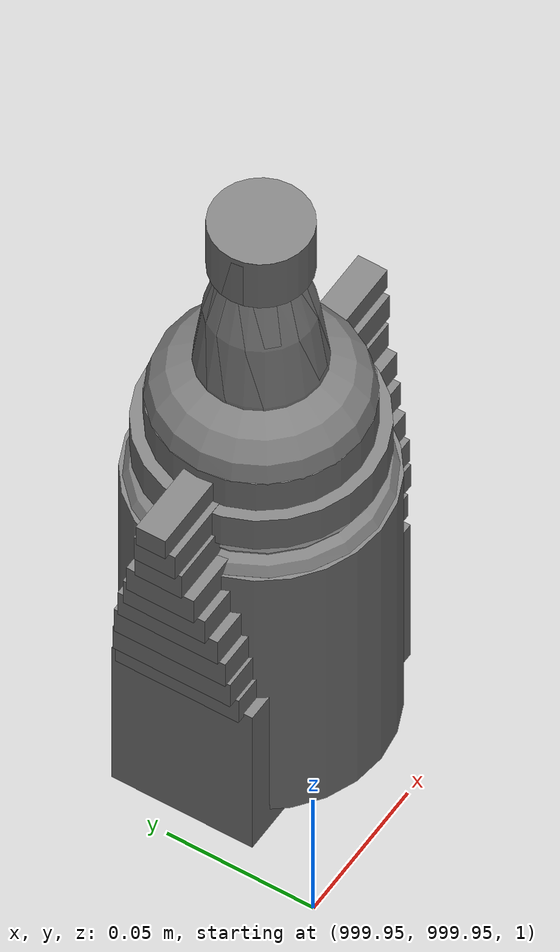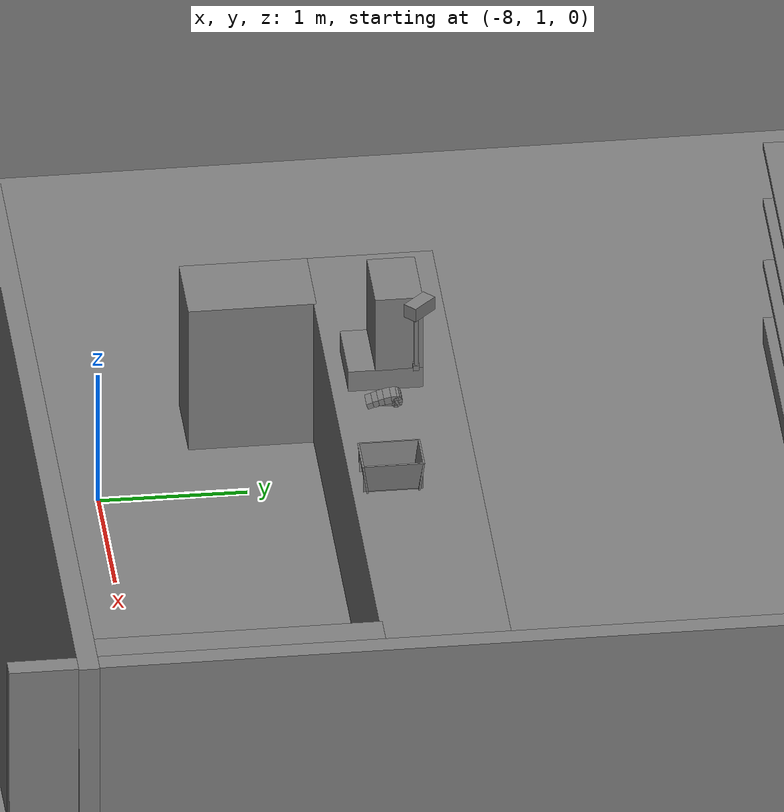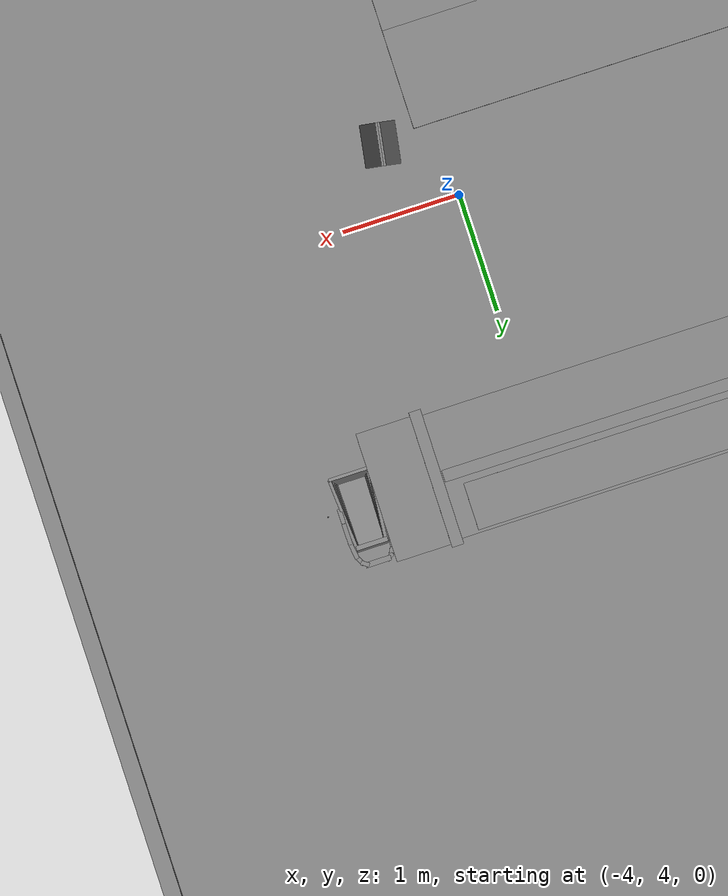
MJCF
<mujoco>
    <option gravity="0.000000000 0.000000000 -9.810000420" timestep="0.0166666" integrator="implicitfast" density="1.225" viscosity="1.8000001e-05" noslip_iterations="10" iterations="100" sdf_iterations="50">
        <flag multiccd="disable"/>
    </option>
    <size memory="1000M"/>
    <compiler coordinate="local"/>
    <worldbody>
        <light cutoff="30" pos="0 1 1" dir="0 -1 -2"/>
        <light cutoff="30" pos="0 -1 1" dir="0 1 -2"/>
        <body pos="-2.436573029 6.404376507 0.137849092" euler="0.000000000 0.000000000 0.000000000" name="openloong_gripper_2f85_fix_base_usda_shoppingtrolley_01">
            <geom contype="1" conaffinity="1" density="1000" type="box" material="" rgba="0.500000000 0.500000000 0.500000000 1.000000000" solimp="0.899999976 0.949999988 0.001000000" friction="1.000000000 0.005000000 0.000100000" solref="0.020000000 1.000000000" margin="0" condim="3" group="0" pos="-0.169898406 -0.178061336 0.864131629" quat="0.916343808 -0.400392294 -0.000000045 0.000000030" size="0.017999999 0.022499999 0.089999996" name="openloong_gripper_2f85_fix_base_usda_geom_B7764E20_76CF_493F_9913_3EFB8E99FC55"/>
            <geom contype="1" conaffinity="1" density="1000" type="box" material="" rgba="0.500000000 0.500000000 0.500000000 1.000000000" solimp="0.899999976 0.949999988 0.001000000" friction="1.000000000 0.005000000 0.000100000" solref="0.020000000 1.000000000" margin="0" condim="3" group="0" pos="-0.107458733 0.238907143 0.911498845" quat="0.634576976 0.622505128 -0.330067992 -0.317575932" size="0.017999999 0.022499999 0.035999998" name="openloong_gripper_2f85_fix_base_usda_geom_4019DDA7_879C_43A6_823C_83F10F2B4DF0"/>
            <geom contype="1" conaffinity="1" density="1000" type="box" material="" rgba="0.500000000 0.500000000 0.500000000 1.000000000" solimp="0.899999976 0.949999988 0.001000000" friction="1.000000000 0.005000000 0.000100000" solref="0.020000000 1.000000000" margin="0" condim="3" group="0" pos="-0.005004787 0.248085022 0.912686050" quat="1.000000000 0.000000000 0.000000000 0.000000000" size="0.107999995 0.022499999 0.022499999" name="openloong_gripper_2f85_fix_base_usda_geom_AF96D825_592C_4EBA_90B6_257EA31313C6"/>
            <geom contype="1" conaffinity="1" density="1000" type="box" material="" rgba="0.500000000 0.500000000 0.500000000 1.000000000" solimp="0.899999976 0.949999988 0.001000000" friction="1.000000000 0.005000000 0.000100000" solref="0.020000000 1.000000000" margin="0" condim="3" group="0" pos="0.131482959 -0.182533979 0.598989725" quat="0.996607125 0.055331629 0.059003670 0.015205893" size="0.013499999 0.287999988 0.053999998" name="openloong_gripper_2f85_fix_base_usda_geom_044D3943_CB4E_4035_8354_61F33D9E11E5"/>
            <geom contype="1" conaffinity="1" density="1000" type="box" material="" rgba="0.500000000 0.500000000 0.500000000 1.000000000" solimp="0.899999976 0.949999988 0.001000000" friction="1.000000000 0.005000000 0.000100000" solref="0.020000000 1.000000000" margin="0" condim="3" group="0" pos="-0.000005364 0.100332208 0.734785020" quat="0.999668717 0.025737956 -0.000000010 0.000000000" size="0.135000005 0.019800000 0.152999997" name="openloong_gripper_2f85_fix_base_usda_geom_733C5F7E_DD00_4077_9023_E9B3DFB9CCA6"/>
            <geom contype="1" conaffinity="1" density="1000" type="box" material="" rgba="0.500000000 0.500000000 0.500000000 1.000000000" solimp="0.899999976 0.949999988 0.001000000" friction="1.000000000 0.005000000 0.000100000" solref="0.020000000 1.000000000" margin="0" condim="3" group="0" pos="-0.126757339 -0.182533979 0.598989725" quat="0.996607184 0.055331606 -0.059003651 -0.015205891" size="0.013499999 0.287999988 0.053999998" name="openloong_gripper_2f85_fix_base_usda_geom_8BC33B2F_3F2E_402A_ACEE_EFF4C0CBD556"/>
            <geom contype="1" conaffinity="1" density="1000" type="box" material="" rgba="0.500000000 0.500000000 0.500000000 1.000000000" solimp="0.899999976 0.949999988 0.001000000" friction="1.000000000 0.005000000 0.000100000" solref="0.020000000 1.000000000" margin="0" condim="3" group="0" pos="-0.134013891 0.200098798 0.912192523" quat="0.694057047 0.679413557 -0.172947660 -0.163618833" size="0.017999999 0.022499999 0.035999998" name="openloong_gripper_2f85_fix_base_usda_geom_461D2B47_0137_4CC1_A8BE_9F5ABD70D1CC"/>
            <geom contype="1" conaffinity="1" density="1000" type="box" material="" rgba="0.500000000 0.500000000 0.500000000 1.000000000" solimp="0.899999976 0.949999988 0.001000000" friction="1.000000000 0.005000000 0.000100000" solref="0.020000000 1.000000000" margin="0" condim="3" group="0" pos="0.141839072 -0.191051379 0.702451229" quat="0.997147262 0.056065105 0.045779929 0.021407485" size="0.013499999 0.287999988 0.053999998" name="openloong_gripper_2f85_fix_base_usda_geom_35C13FB8_4D50_4D34_96FA_81EBEC34E17E"/>
            <geom contype="1" conaffinity="1" density="1000" type="box" material="" rgba="0.500000000 0.500000000 0.500000000 1.000000000" solimp="0.899999976 0.949999988 0.001000000" friction="1.000000000 0.005000000 0.000100000" solref="0.020000000 1.000000000" margin="0" condim="3" group="0" pos="-0.135714188 -0.191051379 0.694841146" quat="0.997147322 0.056064609 -0.045779683 -0.021407485" size="0.013499999 0.287999988 0.053999998" name="openloong_gripper_2f85_fix_base_usda_geom_9544DC1A_4D54_4985_99AE_DFA2E39FDD29"/>
            <geom contype="1" conaffinity="1" density="1000" type="box" material="" rgba="0.500000000 0.500000000 0.500000000 1.000000000" solimp="0.899999976 0.949999988 0.001000000" friction="1.000000000 0.005000000 0.000100000" solref="0.020000000 1.000000000" margin="0" condim="3" group="0" pos="-0.000004721 -0.174527690 0.560063601" quat="0.996704638 0.081116498 -0.000000004 0.000000000" size="0.126000002 0.287999988 0.009000000" name="openloong_gripper_2f85_fix_base_usda_geom_A4038EB6_CBD3_4726_B862_AD6301325A55"/>
            <geom contype="1" conaffinity="1" density="1000" type="box" material="" rgba="0.500000000 0.500000000 0.500000000 1.000000000" solimp="0.899999976 0.949999988 0.001000000" friction="1.000000000 0.005000000 0.000100000" solref="0.020000000 1.000000000" margin="0" condim="3" group="0" pos="0.134013891 0.200098798 0.912192523" quat="0.692574680 -0.680924535 -0.166899428 0.169783980" size="0.017999999 0.022499999 0.035999998" name="openloong_gripper_2f85_fix_base_usda_geom_E212A2EA_9438_4828_8A4A_E167370F14DE"/>
            <geom contype="1" conaffinity="1" density="1000" type="box" material="" rgba="0.500000000 0.500000000 0.500000000 1.000000000" solimp="0.899999976 0.949999988 0.001000000" friction="1.000000000 0.005000000 0.000100000" solref="0.020000000 1.000000000" margin="0" condim="3" group="0" pos="-0.012634277 -0.174527690 -0.088243507" quat="1.000000000 0.000000000 -0.000000004 0.000000000" size="0.135000005 0.287999988 0.044999998" name="openloong_gripper_2f85_fix_base_usda_geom_DFB5520D_4CD4_4B19_BCA1_C1FBA3A7D4FB"/>
            <geom contype="1" conaffinity="1" density="1000" type="box" material="" rgba="0.500000000 0.500000000 0.500000000 1.000000000" solimp="0.899999976 0.949999988 0.001000000" friction="1.000000000 0.005000000 0.000100000" solref="0.020000000 1.000000000" margin="0" condim="3" group="0" pos="-0.142927840 -0.199506134 0.784674108" quat="0.998421252 0.016904408 -0.027109101 -0.046199299" size="0.013499999 0.305999994 0.063000001" name="openloong_gripper_2f85_fix_base_usda_geom_BC584EF5_E8E3_40A3_82C0_E7699CFF8C70"/>
            <geom contype="1" conaffinity="1" density="1000" type="box" material="" rgba="0.500000000 0.500000000 0.500000000 1.000000000" solimp="0.899999976 0.949999988 0.001000000" friction="1.000000000 0.005000000 0.000100000" solref="0.020000000 1.000000000" margin="0" condim="3" group="0" pos="-0.169898406 -0.043119621 0.915120542" quat="0.687021017 0.726584017 -0.005590606 -0.006832919" size="0.017999999 0.022499999 0.089999996" name="openloong_gripper_2f85_fix_base_usda_geom_A1B3BBC4_AFF7_41F0_B679_8070EA54FDFD"/>
            <geom contype="1" conaffinity="1" density="1000" type="box" material="" rgba="0.500000000 0.500000000 0.500000000 1.000000000" solimp="0.899999976 0.949999988 0.001000000" friction="1.000000000 0.005000000 0.000100000" solref="0.020000000 1.000000000" margin="0" condim="3" group="0" pos="-0.000006008 -0.484932661 0.670727849" quat="0.997585475 0.069449045 -0.000000004 -0.000000089" size="0.179999992 0.013499999 0.170999989" name="openloong_gripper_2f85_fix_base_usda_geom_CBBCFFAA_E715_4D33_9CBD_35C54D100741"/>
            <geom contype="1" conaffinity="1" density="1000" type="box" material="" rgba="0.500000000 0.500000000 0.500000000 1.000000000" solimp="0.899999976 0.949999988 0.001000000" friction="1.000000000 0.005000000 0.000100000" solref="0.020000000 1.000000000" margin="0" condim="3" group="0" pos="0.160832971 0.103427693 0.910528183" quat="0.711112797 -0.700149298 -0.042821646 0.047705106" size="0.017999999 0.022499999 0.071999997" name="openloong_gripper_2f85_fix_base_usda_geom_138BC4F8_EBFF_4995_8BE4_B3EBE0A4AA38"/>
            <geom contype="1" conaffinity="1" density="1000" type="box" material="" rgba="0.500000000 0.500000000 0.500000000 1.000000000" solimp="0.899999976 0.949999988 0.001000000" friction="1.000000000 0.005000000 0.000100000" solref="0.020000000 1.000000000" margin="0" condim="3" group="0" pos="-0.160832763 0.103427693 0.910528183" quat="0.711469591 0.699786782 -0.048386075 -0.042050660" size="0.017999999 0.022499999 0.071999997" name="openloong_gripper_2f85_fix_base_usda_geom_1DCDFB5A_36DC_46CD_B90A_BD697E0E33EC"/>
            <geom contype="1" conaffinity="1" density="1000" type="box" material="" rgba="0.500000000 0.500000000 0.500000000 1.000000000" solimp="0.899999976 0.949999988 0.001000000" friction="1.000000000 0.005000000 0.000100000" solref="0.020000000 1.000000000" margin="0" condim="3" group="0" pos="0.169898629 -0.178061336 0.864131629" quat="0.916343808 -0.400392294 -0.000000045 0.000000030" size="0.017999999 0.022499999 0.089999996" name="openloong_gripper_2f85_fix_base_usda_geom_A595C957_BF31_4257_AD17_EDA64785F46B"/>
            <geom contype="1" conaffinity="1" density="1000" type="box" material="" rgba="0.500000000 0.500000000 0.500000000 1.000000000" solimp="0.899999976 0.949999988 0.001000000" friction="1.000000000 0.005000000 0.000100000" solref="0.020000000 1.000000000" margin="0" condim="3" group="0" pos="0.103667587 0.233050480 0.912927270" quat="0.634205043 -0.622199059 -0.324503720 0.324576139" size="0.017999999 0.022499999 0.035999998" name="openloong_gripper_2f85_fix_base_usda_geom_C69F7093_6643_4E5F_95BD_E9DF0249E5B8"/>
            <geom contype="1" conaffinity="1" density="1000" type="box" material="" rgba="0.500000000 0.500000000 0.500000000 1.000000000" solimp="0.899999976 0.949999988 0.001000000" friction="1.000000000 0.005000000 0.000100000" solref="0.020000000 1.000000000" margin="0" condim="3" group="0" pos="0.169898629 -0.043119621 0.915120542" quat="0.687029123 -0.726576388 -0.006509603 0.005963952" size="0.017999999 0.022499999 0.089999996" name="openloong_gripper_2f85_fix_base_usda_geom_B2A42275_FE9C_4217_BF29_B4A1DB970220"/>
            <geom contype="1" conaffinity="1" density="1000" type="box" material="" rgba="0.500000000 0.500000000 0.500000000 1.000000000" solimp="0.899999976 0.949999988 0.001000000" friction="1.000000000 0.005000000 0.000100000" solref="0.020000000 1.000000000" margin="0" condim="3" group="0" pos="0.148195267 -0.199506566 0.782808602" quat="0.998808920 0.017156634 0.026950166 0.036880098" size="0.013499999 0.305999994 0.063000001" name="openloong_gripper_2f85_fix_base_usda_geom_5471C99C_E31D_466B_ADE6_6689B9B475E9"/>
            <freejoint name="openloong_gripper_2f85_fix_base_usda_shoppingtrolley_01_joint"/>
            <site size="0.005000000 0.005000000 0.005000000" rgba="0.500000000 0.500000000 0.500000000 1.000000000" pos="0.000000000 0.000000000 0.000000000" quat="1.000000000 0.000000000 0.000000000 0.000000000" group="0" type="sphere" name="openloong_gripper_2f85_fix_base_usda_shoppingtrolley_01"/>
        </body>
        <body pos="1000.000000000 1000.000000000 1.000000000" euler="0.000000000 0.000000000 0.000000000" name="openloong_gripper_2f85_fix_base_usda_jar_01">
            <geom contype="1" conaffinity="1" density="1000" type="box" material="" rgba="0.500000000 0.500000000 0.500000000 1.000000000" solimp="0.899999976 0.949999988 0.001000000" friction="1.000000000 0.005000000 0.000100000" solref="0.020000000 1.000000000" margin="0" condim="3" group="0" pos="0.000000000 0.000000000 0.006158113" quat="1.000000000 0.000000000 0.000000000 0.000000000" size="0.020000000 0.020000000 0.005000000" name="openloong_gripper_2f85_fix_base_usda_geom_5A94FED8_60BD_47E6_866C_710A734D0E0D"/>
            <geom contype="1" conaffinity="1" density="1000" type="cylinder" material="" rgba="0.500000000 0.500000000 0.500000000 1.000000000" solimp="0.899999976 0.949999988 0.001000000" friction="1.000000000 0.005000000 0.000100000" solref="0.020000000 1.000000000" margin="0" condim="3" group="0" pos="0.000000000 0.000000000 0.062744498" quat="1.000000000 0.000000000 0.000000000 0.000000000" size="0.041000001 0.052999999 1.000000000" name="openloong_gripper_2f85_fix_base_usda_geom_960089D6_652C_4156_A364_46AD196B3B92"/>
            <geom contype="1" conaffinity="1" density="1000" type="ellipsoid" material="" rgba="0.500000000 0.500000000 0.500000000 1.000000000" solimp="0.899999976 0.949999988 0.001000000" friction="1.000000000 0.005000000 0.000100000" solref="0.020000000 1.000000000" margin="0" condim="3" group="0" pos="0.000000000 0.000000000 0.122252703" quat="1.000000000 0.000000000 0.000000000 0.000000000" size="0.035999998 0.035999998 0.010000000" name="openloong_gripper_2f85_fix_base_usda_geom_8D2E059A_7907_40BC_A3A6_753489B1F2D3"/>
            <geom contype="1" conaffinity="1" density="1000" type="cylinder" material="" rgba="0.500000000 0.500000000 0.500000000 1.000000000" solimp="0.899999976 0.949999988 0.001000000" friction="1.000000000 0.005000000 0.000100000" solref="0.020000000 1.000000000" margin="0" condim="3" group="0" pos="0.000000000 0.000000000 0.015747190" quat="1.000000000 0.000000000 0.000000000 0.000000000" size="0.035000000 0.010000000 1.000000000" name="openloong_gripper_2f85_fix_base_usda_geom_0245D6E9_4016_4DDC_BD07_81A8872C01B2"/>
            <geom contype="1" conaffinity="1" density="1000" type="ellipsoid" material="" rgba="0.500000000 0.500000000 0.500000000 1.000000000" solimp="0.899999976 0.949999988 0.001000000" friction="1.000000000 0.005000000 0.000100000" solref="0.020000000 1.000000000" margin="0" condim="3" group="0" pos="0.000000000 0.000000000 0.115815401" quat="1.000000000 0.000000000 0.000000000 0.000000000" size="0.039999999 0.039999999 0.010000000" name="openloong_gripper_2f85_fix_base_usda_geom_275B75DC_4AC5_4A8C_AF9A_503613F6AD8A"/>
            <geom contype="1" conaffinity="1" density="1000" type="cylinder" material="" rgba="0.500000000 0.500000000 0.500000000 1.000000000" solimp="0.899999976 0.949999988 0.001000000" friction="1.000000000 0.005000000 0.000100000" solref="0.020000000 1.000000000" margin="0" condim="3" group="0" pos="0.000000000 0.000000000 0.133183479" quat="1.000000000 0.000000000 0.000000000 0.000000000" size="0.037999999 0.006500000 1.000000000" name="openloong_gripper_2f85_fix_base_usda_geom_760BC228_2354_432C_971B_DA0835C9D6FD"/>
            <freejoint name="openloong_gripper_2f85_fix_base_usda_jar_01_joint"/>
            <site size="0.005000000 0.005000000 0.005000000" rgba="0.500000000 0.500000000 0.500000000 1.000000000" pos="0.000000000 0.000000000 0.000000000" quat="1.000000000 0.000000000 0.000000000 0.000000000" group="0" type="sphere" name="openloong_gripper_2f85_fix_base_usda_jar_01site"/>
        </body>
        <body pos="1000.000000000 1000.000000000 1.000000000" euler="0.000000000 0.000000000 0.000000000" name="openloong_gripper_2f85_fix_base_usda_bottle_red">
            <geom contype="1" conaffinity="1" density="1000" type="ellipsoid" material="" rgba="0.500000000 0.500000000 0.500000000 1.000000000" solimp="0.899999976 0.949999988 0.001000000" friction="1.000000000 0.005000000 0.000100000" solref="0.020000000 1.000000000" margin="0" condim="3" group="0" pos="0.000000000 0.000000000 0.144284487" quat="1.000000000 0.000000000 0.000000000 0.000000000" size="0.021000000 0.021000000 0.079999998" name="openloong_gripper_2f85_fix_base_usda_geom_2F9905DE_9270_4BFA_AB3F_0D46B77254CB"/>
            <geom contype="1" conaffinity="1" density="1000" type="cylinder" material="" rgba="0.500000000 0.500000000 0.500000000 1.000000000" solimp="0.899999976 0.949999988 0.001000000" friction="1.000000000 0.005000000 0.000100000" solref="0.020000000 1.000000000" margin="0" condim="3" group="0" pos="0.000000000 0.000000000 0.220618963" quat="1.000000000 0.000000000 0.000000000 0.000000000" size="0.016000001 0.010000000 1.000000000" name="openloong_gripper_2f85_fix_base_usda_geom_D8A16EDD_9FD8_4278_82D2_F34023362504"/>
            <geom contype="1" conaffinity="1" density="1000" type="ellipsoid" material="" rgba="0.500000000 0.500000000 0.500000000 1.000000000" solimp="0.899999976 0.949999988 0.001000000" friction="1.000000000 0.005000000 0.000100000" solref="0.020000000 1.000000000" margin="0" condim="3" group="0" pos="0.000000000 0.000000000 0.118945479" quat="1.000000000 0.000000000 0.000000000 0.000000000" size="0.030999999 0.030999999 0.029999999" name="openloong_gripper_2f85_fix_base_usda_geom_26D358F2_A77E_4F82_8D48_D0B034B53570"/>
            <geom contype="1" conaffinity="1" density="1000" type="box" material="" rgba="0.500000000 0.500000000 0.500000000 1.000000000" solimp="0.899999976 0.949999988 0.001000000" friction="1.000000000 0.005000000 0.000100000" solref="0.020000000 1.000000000" margin="0" condim="3" group="0" pos="0.000000000 0.000000000 0.002189159" quat="1.000000000 0.000000000 0.000000000 0.000000000" size="0.020000000 0.020000000 0.003000000" name="openloong_gripper_2f85_fix_base_usda_geom_8D8FB219_F043_47DA_AE4F_E849A47D2A64"/>
            <geom contype="1" conaffinity="1" density="1000" type="cylinder" material="" rgba="0.500000000 0.500000000 0.500000000 1.000000000" solimp="0.899999976 0.949999988 0.001000000" friction="1.000000000 0.005000000 0.000100000" solref="0.020000000 1.000000000" margin="0" condim="3" group="0" pos="0.000000000 -0.000366211 0.060884237" quat="1.000000000 0.000000000 0.000000000 0.000000000" size="0.030999999 0.057999998 1.000000000" name="openloong_gripper_2f85_fix_base_usda_geom_E5302877_5E01_42FB_B075_A8ADAE28BE24"/>
            <freejoint name="openloong_gripper_2f85_fix_base_usda_bottle_red_joint"/>
            <site size="0.005000000 0.005000000 0.005000000" rgba="0.500000000 0.500000000 0.500000000 1.000000000" pos="0.000000000 0.000000000 0.000000000" quat="0.999961913 0.008726535 0.000000000 0.000000000" group="0" type="sphere" name="openloong_gripper_2f85_fix_base_usda_bottle_redsite"/>
        </body>
        <body pos="1000.000000000 1000.000000000 1.000000000" euler="0.000000000 0.000000000 0.000000000" name="openloong_gripper_2f85_fix_base_usda_can">
            <geom contype="1" conaffinity="1" density="1000" type="cylinder" material="" rgba="0.500000000 0.500000000 0.500000000 1.000000000" solimp="0.899999976 0.949999988 0.001000000" friction="1.000000000 0.005000000 0.000100000" solref="0.020000000 1.000000000" margin="0" condim="3" group="0" pos="0.000000000 0.000000000 0.079676986" quat="1.000000000 0.000000000 0.000000000 0.000000000" size="0.034000002 0.071999997 1.000000000" name="openloong_gripper_2f85_fix_base_usda_geom_5E26156F_EB75_43B5_BBFB_5C3B9E69BFD7"/>
            <geom contype="1" conaffinity="1" density="1000" type="ellipsoid" material="" rgba="0.500000000 0.500000000 0.500000000 1.000000000" solimp="0.899999976 0.949999988 0.001000000" friction="1.000000000 0.005000000 0.000100000" solref="0.020000000 1.000000000" margin="0" condim="3" group="0" pos="0.000000000 0.000000000 0.151854277" quat="1.000000000 0.000000000 0.000000000 0.000000000" size="0.034000002 0.034000002 0.020000000" name="openloong_gripper_2f85_fix_base_usda_geom_45311DC2_C913_41E0_BC0E_856CFE3E0310"/>
            <geom contype="1" conaffinity="1" density="1000" type="box" material="" rgba="0.500000000 0.500000000 0.500000000 1.000000000" solimp="0.899999976 0.949999988 0.001000000" friction="1.000000000 0.005000000 0.000100000" solref="0.020000000 1.000000000" margin="0" condim="3" group="0" pos="0.000000000 0.000000000 0.004777670" quat="1.000000000 0.000000000 0.000000000 0.000000000" size="0.020000000 0.020000000 0.005000000" name="openloong_gripper_2f85_fix_base_usda_geom_BA09CA76_4ADF_44FD_A76A_8BC0FA34DF43"/>
            <freejoint name="openloong_gripper_2f85_fix_base_usda_can_joint"/>
            <site size="0.005000000 0.005000000 0.005000000" rgba="0.500000000 0.500000000 0.500000000 1.000000000" pos="0.000000000 0.000000000 0.000000000" quat="1.000000000 0.000000000 0.000000000 0.000000000" group="0" type="sphere" name="openloong_gripper_2f85_fix_base_usda_cansite"/>
        </body>
        <body pos="-2.132212639 5.791541100 1.801488638" euler="22.462999344 51.337543488 132.117324829" mocap="true" name="spotlight4_SpotLight"/>
        <body pos="-1.908498287 6.601111889 1.806894898" euler="-56.661167145 -31.445079803 -38.282375336" mocap="true" name="spotlight2_SpotLight"/>
        <body pos="1000.000000000 1000.000000000 1.000000000" euler="0.000000000 0.000000000 0.000000000" name="openloong_gripper_2f85_fix_base_usda_salt">
            <geom contype="1" conaffinity="1" density="1000" type="box" material="" rgba="0.500000000 0.500000000 0.500000000 1.000000000" solimp="0.899999976 0.949999988 0.001000000" friction="1.000000000 0.005000000 0.000100000" solref="0.020000000 1.000000000" margin="0" condim="3" group="0" pos="0.000305176 0.000000000 0.084862232" quat="1.000000000 0.000000000 0.000000000 0.000000000" size="0.048999999 0.018999999 0.005000000" name="openloong_gripper_2f85_fix_base_usda_geom_5E3E018B_8F45_4D7A_A8C1_3B14A440FAD1"/>
            <geom contype="1" conaffinity="1" density="1000" type="box" material="" rgba="0.500000000 0.500000000 0.500000000 1.000000000" solimp="0.899999976 0.949999988 0.001000000" friction="1.000000000 0.005000000 0.000100000" solref="0.020000000 1.000000000" margin="0" condim="3" group="0" pos="0.000305176 0.000000000 0.104564309" quat="1.000000000 0.000000000 0.000000000 0.000000000" size="0.052000001 0.014000000 0.005000000" name="openloong_gripper_2f85_fix_base_usda_geom_D4B78544_CBFD_4D1E_9BCA_2F6E3DC92377"/>
            <geom contype="1" conaffinity="1" density="1000" type="box" material="" rgba="0.500000000 0.500000000 0.500000000 1.000000000" solimp="0.899999976 0.949999988 0.001000000" friction="1.000000000 0.005000000 0.000100000" solref="0.020000000 1.000000000" margin="0" condim="3" group="0" pos="0.000305176 0.000000000 0.114487171" quat="1.000000000 0.000000000 0.000000000 0.000000000" size="0.054000001 0.011500000 0.005000000" name="openloong_gripper_2f85_fix_base_usda_geom_DC37D156_C6B4_4066_A36C_E0B53BC35A7A"/>
            <geom contype="1" conaffinity="1" density="1000" type="box" material="" rgba="0.500000000 0.500000000 0.500000000 1.000000000" solimp="0.899999976 0.949999988 0.001000000" friction="1.000000000 0.005000000 0.000100000" solref="0.020000000 1.000000000" margin="0" condim="3" group="0" pos="0.000305176 0.000000000 0.075103164" quat="1.000000000 0.000000000 0.000000000 0.000000000" size="0.048000000 0.020000000 0.005000000" name="openloong_gripper_2f85_fix_base_usda_geom_8354B6D9_01CE_446C_856C_8D79D6E9F60B"/>
            <geom contype="1" conaffinity="1" density="1000" type="box" material="" rgba="0.500000000 0.500000000 0.500000000 1.000000000" solimp="0.899999976 0.949999988 0.001000000" friction="1.000000000 0.005000000 0.000100000" solref="0.020000000 1.000000000" margin="0" condim="3" group="0" pos="0.000305176 0.000000000 0.134892464" quat="1.000000000 0.000000000 0.000000000 0.000000000" size="0.057000000 0.007000000 0.005000000" name="openloong_gripper_2f85_fix_base_usda_geom_57A27401_323D_488E_A3D3_6C07551E25FF"/>
            <geom contype="1" conaffinity="1" density="1000" type="box" material="" rgba="0.500000000 0.500000000 0.500000000 1.000000000" solimp="0.899999976 0.949999988 0.001000000" friction="1.000000000 0.005000000 0.000100000" solref="0.020000000 1.000000000" margin="0" condim="3" group="0" pos="0.000305176 0.000000000 0.094920278" quat="1.000000000 0.000000000 0.000000000 0.000000000" size="0.050000001 0.017000001 0.005000000" name="openloong_gripper_2f85_fix_base_usda_geom_7F11F91C_0DA5_43FD_907C_CF0B64AEA1EC"/>
            <geom contype="1" conaffinity="1" density="1000" type="box" material="" rgba="0.500000000 0.500000000 0.500000000 1.000000000" solimp="0.899999976 0.949999988 0.001000000" friction="1.000000000 0.005000000 0.000100000" solref="0.020000000 1.000000000" margin="0" condim="3" group="0" pos="0.000305176 0.000000000 0.065204859" quat="1.000000000 0.000000000 0.000000000 0.000000000" size="0.045000002 0.021000000 0.005000000" name="openloong_gripper_2f85_fix_base_usda_geom_3EEFC334_D13A_4115_B1D2_5ECF7BC55E0B"/>
            <geom contype="1" conaffinity="1" density="1000" type="box" material="" rgba="0.500000000 0.500000000 0.500000000 1.000000000" solimp="0.899999976 0.949999988 0.001000000" friction="1.000000000 0.005000000 0.000100000" solref="0.020000000 1.000000000" margin="0" condim="3" group="0" pos="0.000305176 0.000000000 0.144135714" quat="1.000000000 0.000000000 0.000000000 0.000000000" size="0.059000000 0.005000000 0.004000000" name="openloong_gripper_2f85_fix_base_usda_geom_A4E706BC_7D88_4D87_AD4A_C669EE8FFD18"/>
            <geom contype="1" conaffinity="1" density="1000" type="box" material="" rgba="0.500000000 0.500000000 0.500000000 1.000000000" solimp="0.899999976 0.949999988 0.001000000" friction="1.000000000 0.005000000 0.000100000" solref="0.020000000 1.000000000" margin="0" condim="3" group="0" pos="0.000000000 0.000000000 0.031593561" quat="1.000000000 0.000000000 0.000000000 0.000000000" size="0.041999999 0.024000000 0.029999999" name="openloong_gripper_2f85_fix_base_usda_geom_D26480EA_1DD1_40A1_9061_A7266C53499E"/>
            <geom contype="1" conaffinity="1" density="1000" type="box" material="" rgba="0.500000000 0.500000000 0.500000000 1.000000000" solimp="0.899999976 0.949999988 0.001000000" friction="1.000000000 0.005000000 0.000100000" solref="0.020000000 1.000000000" margin="0" condim="3" group="0" pos="0.000305176 0.000000000 0.124608755" quat="1.000000000 0.000000000 0.000000000 0.000000000" size="0.055000000 0.008000000 0.005000000" name="openloong_gripper_2f85_fix_base_usda_geom_C98CC159_1BE4_495D_8C8B_13D431B5D4FC"/>
            <freejoint name="openloong_gripper_2f85_fix_base_usda_salt_joint"/>
            <site size="0.005000000 0.005000000 0.005000000" rgba="0.500000000 0.500000000 0.500000000 1.000000000" pos="0.000000000 0.000000000 0.000000000" quat="1.000000000 0.000000000 0.000000000 0.000000000" group="0" type="sphere" name="openloong_gripper_2f85_fix_base_usda_saltsite"/>
        </body>
        <body pos="-2.154065371 6.343229771 1.696751595" euler="-100.515808105 46.426414490 50.239700317" mocap="true" name="spotlight3_SpotLight"/>
        <body pos="1000.000000000 1000.000000000 1.000000000" euler="0.000000000 0.000000000 0.000000000" name="openloong_gripper_2f85_fix_base_usda_bottle_blue">
            <geom contype="1" conaffinity="1" density="1000" type="ellipsoid" material="" rgba="0.500000000 0.500000000 0.500000000 1.000000000" solimp="0.899999976 0.949999988 0.001000000" friction="1.000000000 0.005000000 0.000100000" solref="0.020000000 1.000000000" margin="0" condim="3" group="0" pos="0.000000000 0.000000000 0.118920922" quat="1.000000000 0.000000000 0.000000000 0.000000000" size="0.030999999 0.030999999 0.029999999" name="openloong_gripper_2f85_fix_base_usda_geom_C3ED8EEA_1989_4808_82BC_3A0EA7770A2F"/>
            <geom contype="1" conaffinity="1" density="1000" type="box" material="" rgba="0.500000000 0.500000000 0.500000000 1.000000000" solimp="0.899999976 0.949999988 0.001000000" friction="1.000000000 0.005000000 0.000100000" solref="0.020000000 1.000000000" margin="0" condim="3" group="0" pos="0.000000000 0.000000000 0.002164602" quat="1.000000000 0.000000000 0.000000000 0.000000000" size="0.020000000 0.020000000 0.003000000" name="openloong_gripper_2f85_fix_base_usda_geom_A50DBE17_7478_41F9_973F_879D0351C88D"/>
            <geom contype="1" conaffinity="1" density="1000" type="cylinder" material="" rgba="0.500000000 0.500000000 0.500000000 1.000000000" solimp="0.899999976 0.949999988 0.001000000" friction="1.000000000 0.005000000 0.000100000" solref="0.020000000 1.000000000" margin="0" condim="3" group="0" pos="0.000000000 -0.000366211 0.060859680" quat="1.000000000 0.000000000 0.000000000 0.000000000" size="0.030999999 0.057999998 1.000000000" name="openloong_gripper_2f85_fix_base_usda_geom_4273334C_3F84_41DF_91CB_D4DDAA44A40C"/>
            <geom contype="1" conaffinity="1" density="1000" type="cylinder" material="" rgba="0.500000000 0.500000000 0.500000000 1.000000000" solimp="0.899999976 0.949999988 0.001000000" friction="1.000000000 0.005000000 0.000100000" solref="0.020000000 1.000000000" margin="0" condim="3" group="0" pos="0.000000000 0.000000000 0.220594406" quat="1.000000000 0.000000000 0.000000000 0.000000000" size="0.016000001 0.010000000 1.000000000" name="openloong_gripper_2f85_fix_base_usda_geom_9DEC0127_6E09_414E_93FB_D0280F42E2D7"/>
            <geom contype="1" conaffinity="1" density="1000" type="ellipsoid" material="" rgba="0.500000000 0.500000000 0.500000000 1.000000000" solimp="0.899999976 0.949999988 0.001000000" friction="1.000000000 0.005000000 0.000100000" solref="0.020000000 1.000000000" margin="0" condim="3" group="0" pos="0.000000000 0.000000000 0.144259930" quat="1.000000000 0.000000000 0.000000000 0.000000000" size="0.021000000 0.021000000 0.079999998" name="openloong_gripper_2f85_fix_base_usda_geom_9530EAC9_1D25_4113_9F50_7872961522B7"/>
            <freejoint name="openloong_gripper_2f85_fix_base_usda_bottle_blue_joint"/>
            <site size="0.005000000 0.005000000 0.005000000" rgba="0.500000000 0.500000000 0.500000000 1.000000000" pos="0.000000000 0.000000000 0.000000000" quat="0.999961913 0.008726535 0.000000000 0.000000000" group="0" type="sphere" name="openloong_gripper_2f85_fix_base_usda_bottle_bluesite"/>
        </body>
        <body pos="0.000000000 0.000000000 0.000000000" euler="0.000000000 0.000000000 0.000000000" name="Interactive Objects_Interactive Objects"/>
        <body pos="0.000000000 0.000000000 0.000000000" euler="0.000000000 0.000000000 0.000000000" name=" Static Objects_ Static Objects">
            <geom contype="1" conaffinity="1" density="1000" type="box" material="" rgba="0.500000000 0.500000000 0.500000000 1.000000000" solimp="0.899999976 0.949999988 0.001000000" friction="1.000000000 0.005000000 0.000100000" solref="0.020000000 1.000000000" margin="0" condim="3" group="0" pos="-3.101639986 6.150595188 1.018643856" quat="1.000000000 0.000000000 0.000000000 0.000000000" size="0.050000001 0.579999983 1.019999981" name=" Static Objects_geom_69B655C4_0B7B_4000_8B37_988A758D21AC"/>
            <geom contype="1" conaffinity="1" density="1000" type="box" material="" rgba="0.500000000 0.500000000 0.500000000 1.000000000" solimp="0.899999976 0.949999988 0.001000000" friction="1.000000000 0.005000000 0.000100000" solref="0.020000000 1.000000000" margin="0" condim="3" group="0" pos="-2.825197220 6.153595448 1.115278244" quat="0.707107067 0.000000000 0.000000000 0.707106471" size="0.550000012 0.239999995 0.025000000" name=" Static Objects_geom_B718580B_5F5C_4240_A801_8C0DB6B976F4"/>
            <geom contype="1" conaffinity="1" density="1000" type="box" material="" rgba="0.500000000 0.500000000 0.500000000 1.000000000" solimp="0.899999976 0.949999988 0.001000000" friction="1.000000000 0.005000000 0.000100000" solref="0.020000000 1.000000000" margin="0" condim="3" group="0" pos="-2.825197220 6.153595448 0.097434282" quat="0.707107067 0.000000000 0.000000000 0.707106471" size="0.550000012 0.239999995 0.098999999" name=" Static Objects_geom_D9F3D230_577C_4BB9_BAEF_51F1A732D0BA"/>
            <geom contype="1" conaffinity="1" density="1000" type="box" material="" rgba="0.500000000 0.500000000 0.500000000 1.000000000" solimp="0.899999976 0.949999988 0.001000000" friction="1.000000000 0.005000000 0.000100000" solref="0.020000000 1.000000000" margin="0" condim="3" group="0" pos="-6.293097973 6.153595448 1.114443064" quat="0.707107067 0.000000000 0.000000000 0.707106471" size="0.529999971 3.134999990 0.025000000" name=" Static Objects_geom_AB295E00_B64B_433E_AD9F_C42A452E5D6B"/>
            <geom contype="1" conaffinity="1" density="1000" type="box" material="" rgba="0.500000000 0.500000000 0.500000000 1.000000000" solimp="0.899999976 0.949999988 0.001000000" friction="1.000000000 0.005000000 0.000100000" solref="0.020000000 1.000000000" margin="0" condim="3" group="0" pos="-6.286010742 6.153595448 0.096129179" quat="0.707107067 0.000000000 0.000000000 0.707106471" size="0.529999971 3.134999990 0.098999999" name=" Static Objects_geom_F790B29E_8548_4EC3_8314_DFDF14B9878F"/>
            <geom contype="1" conaffinity="1" density="1000" type="box" material="" rgba="0.500000000 0.500000000 0.500000000 1.000000000" solimp="0.899999976 0.949999988 0.001000000" friction="1.000000000 0.005000000 0.000100000" solref="0.020000000 1.000000000" margin="0" condim="3" group="0" pos="-2.825197220 6.153595448 1.563861728" quat="0.707107067 0.000000000 0.000000000 0.707106471" size="0.550000012 0.239999995 0.025000000" name=" Static Objects_geom_A9825223_4CEE_4409_9AAE_53E4367BF157"/>
            <geom contype="1" conaffinity="1" density="1000" type="box" material="" rgba="0.500000000 0.500000000 0.500000000 1.000000000" solimp="0.899999976 0.949999988 0.001000000" friction="1.000000000 0.005000000 0.000100000" solref="0.020000000 1.000000000" margin="0" condim="3" group="0" pos="-6.311686516 6.153595448 1.018643856" quat="0.707107067 0.000000000 0.000000000 0.707106471" size="0.050000001 3.150000095 1.019999981" name=" Static Objects_geom_BE8A415D_6AF6_40A1_8C41_689969236BC2"/>
            <geom contype="1" conaffinity="1" density="1000" type="box" material="" rgba="0.500000000 0.500000000 0.500000000 1.000000000" solimp="0.899999976 0.949999988 0.001000000" friction="1.000000000 0.005000000 0.000100000" solref="0.020000000 1.000000000" margin="0" condim="3" group="0" pos="-2.825197220 6.153595448 0.629031777" quat="0.707107067 0.000000000 0.000000000 0.707106471" size="0.550000012 0.239999995 0.025000000" name=" Static Objects_geom_AC8DFA8D_47DA_449C_A52B_43F815DCEB93"/>
            <geom contype="1" conaffinity="1" density="1000" type="box" material="" rgba="0.500000000 0.500000000 0.500000000 1.000000000" solimp="0.899999976 0.949999988 0.001000000" friction="1.000000000 0.005000000 0.000100000" solref="0.020000000 1.000000000" margin="0" condim="3" group="0" pos="-6.286010742 6.153595448 1.563861728" quat="0.707107067 0.000000000 0.000000000 0.707106471" size="0.529999971 3.134999990 0.025000000" name=" Static Objects_geom_55F3071B_DE7C_4BD2_BCB0_5F9D6ABE9F37"/>
            <geom contype="1" conaffinity="1" density="1000" type="box" material="" rgba="0.500000000 0.500000000 0.500000000 1.000000000" solimp="0.899999976 0.949999988 0.001000000" friction="1.000000000 0.005000000 0.000100000" solref="0.020000000 1.000000000" margin="0" condim="3" group="0" pos="-6.286010742 6.153595448 0.629031777" quat="0.707107067 0.000000000 0.000000000 0.707106471" size="0.529999971 3.134999990 0.025000000" name=" Static Objects_geom_8463A831_6A6C_4F52_91C1_CAA5BD7F4A59"/>
            <geom contype="1" conaffinity="1" density="1000" type="box" material="" rgba="0.500000000 0.500000000 0.500000000 1.000000000" solimp="0.899999976 0.949999988 0.001000000" friction="1.000000000 0.005000000 0.000100000" solref="0.020000000 1.000000000" margin="0" condim="3" group="0" pos="-7.719123363 2.867671013 1.173410416" quat="1.000000000 0.000000000 0.000000000 0.000000000" size="0.250000000 0.250000000 0.079999998" name=" Static Objects_geom_4DD34A37_BEB1_4CB1_AD48_1E4B2AD61F58"/>
            <geom contype="1" conaffinity="1" density="1000" type="box" material="" rgba="0.500000000 0.500000000 0.500000000 1.000000000" solimp="0.899999976 0.949999988 0.001000000" friction="1.000000000 0.005000000 0.000100000" solref="0.020000000 1.000000000" margin="0" condim="3" group="0" pos="-7.408766270 3.088089943 1.776644945" quat="0.928051054 0.000000000 0.000000000 0.372453064" size="0.050000001 0.100000001 0.050000001" name=" Static Objects_geom_62131CBF_C9B8_4C02_B304_6E7A966130DB"/>
            <geom contype="1" conaffinity="1" density="1000" type="box" material="" rgba="0.500000000 0.500000000 0.500000000 1.000000000" solimp="0.899999976 0.949999988 0.001000000" friction="1.000000000 0.005000000 0.000100000" solref="0.020000000 1.000000000" margin="0" condim="3" group="0" pos="-7.719123363 2.958004713 1.530241251" quat="1.000000000 0.000000000 0.000000000 0.000000000" size="0.250000000 0.159999996 0.280000001" name=" Static Objects_geom_1EF8DD54_2B27_4946_BD3A_DE9EFBF44EFD"/>
            <geom contype="1" conaffinity="1" density="1000" type="cylinder" material="" rgba="0.500000000 0.500000000 0.500000000 1.000000000" solimp="0.899999976 0.949999988 0.001000000" friction="1.000000000 0.005000000 0.000100000" solref="0.020000000 1.000000000" margin="0" condim="3" group="0" pos="-7.427312374 3.069516420 1.502544641" quat="0.928051054 0.000000000 0.000000000 0.372453064" size="0.015000000 0.230000004 0.100000001" name=" Static Objects_geom_50451FC4_BB08_42E4_A529_D6DB27A864C4"/>
            <geom contype="1" conaffinity="1" density="1000" type="box" material="" rgba="0.500000000 0.500000000 0.500000000 1.000000000" solimp="0.899999976 0.949999988 0.001000000" friction="1.000000000 0.005000000 0.000100000" solref="0.020000000 1.000000000" margin="0" condim="3" group="0" pos="-7.437745571 3.067511320 1.289965630" quat="1.000000000 0.000000000 0.000000000 0.000000000" size="0.029999999 0.020000000 0.020000000" name=" Static Objects_geom_DAD330CA_A260_407A_BBB4_A070531F01F9"/>
            <geom contype="1" conaffinity="1" density="1000" type="box" material="" rgba="0.500000000 0.500000000 0.500000000 1.000000000" solimp="0.899999976 0.949999988 0.001000000" friction="1.000000000 0.005000000 0.000100000" solref="0.020000000 1.000000000" margin="0" condim="3" group="0" pos="-9.058088303 6.434794426 1.209077358" quat="1.000000000 0.000000000 0.000000000 0.000000000" size="0.250000000 0.100000001 0.070000000" name=" Static Objects_geom_677EB657_D700_4A1F_B759_0B9568B227AD"/>
            <geom contype="1" conaffinity="1" density="1000" type="box" material="" rgba="0.500000000 0.500000000 0.500000000 1.000000000" solimp="0.899999976 0.949999988 0.001000000" friction="1.000000000 0.005000000 0.000100000" solref="0.020000000 1.000000000" margin="0" condim="3" group="0" pos="-7.886891365 6.459744930 0.352518857" quat="1.000000000 0.000000000 0.000000000 0.000000000" size="1.500000000 0.200000003 0.150000006" name=" Static Objects_geom_EE33F8B9_440D_42CF_8136_03012E1C774D"/>
            <geom contype="1" conaffinity="1" density="1000" type="box" material="" rgba="0.500000000 0.500000000 0.500000000 1.000000000" solimp="0.899999976 0.949999988 0.001000000" friction="1.000000000 0.005000000 0.000100000" solref="0.020000000 1.000000000" margin="0" condim="3" group="0" pos="-9.237723351 6.464855671 1.209077358" quat="1.000000000 0.000000000 0.000000000 0.000000000" size="0.100000001 0.100000001 0.070000000" name=" Static Objects_geom_77BC1655_2E6A_4EFF_9EBE_ECD81A3F0B48"/>
            <geom contype="1" conaffinity="1" density="1000" type="box" material="" rgba="0.500000000 0.500000000 0.500000000 1.000000000" solimp="0.899999976 0.949999988 0.001000000" friction="1.000000000 0.005000000 0.000100000" solref="0.020000000 1.000000000" margin="0" condim="3" group="0" pos="-6.924745083 6.362090111 1.214329123" quat="1.000000000 0.000000000 0.000000000 0.000000000" size="0.200000003 0.100000001 0.075000003" name=" Static Objects_geom_292090FD_7C5A_4E51_B0C5_908AD6C261DC"/>
            <geom contype="1" conaffinity="1" density="1000" type="box" material="" rgba="0.500000000 0.500000000 0.500000000 1.000000000" solimp="0.899999976 0.949999988 0.001000000" friction="1.000000000 0.005000000 0.000100000" solref="0.020000000 1.000000000" margin="0" condim="3" group="0" pos="-4.407354832 6.459744930 1.292199373" quat="1.000000000 0.000000000 0.000000000 0.000000000" size="1.240000010 0.200000003 0.150000006" name=" Static Objects_geom_B0F11292_7BEF_430F_AE4F_628FB79BBB16"/>
            <geom contype="1" conaffinity="1" density="1000" type="box" material="" rgba="0.500000000 0.500000000 0.500000000 1.000000000" solimp="0.899999976 0.949999988 0.001000000" friction="1.000000000 0.005000000 0.000100000" solref="0.020000000 1.000000000" margin="0" condim="3" group="0" pos="-5.611940861 6.318420410 0.350975692" quat="1.000000000 0.000000000 0.000000000 0.000000000" size="0.699999988 0.100000001 0.150000006" name=" Static Objects_geom_547EDAC6_C494_4721_9855_065D9A50FED0"/>
            <geom contype="1" conaffinity="1" density="1000" type="box" material="" rgba="0.500000000 0.500000000 0.500000000 1.000000000" solimp="0.899999976 0.949999988 0.001000000" friction="1.000000000 0.005000000 0.000100000" solref="0.020000000 1.000000000" margin="0" condim="3" group="0" pos="-6.300771236 6.459744930 1.744376063" quat="1.000000000 0.000000000 0.000000000 0.000000000" size="3.000000000 0.200000003 0.150000006" name=" Static Objects_geom_6E3BCF1F_4810_4CB9_9003_67F896E1A59E"/>
            <geom contype="1" conaffinity="1" density="1000" type="box" material="" rgba="0.500000000 0.500000000 0.500000000 1.000000000" solimp="0.899999976 0.949999988 0.001000000" friction="1.000000000 0.005000000 0.000100000" solref="0.020000000 1.000000000" margin="0" condim="3" group="0" pos="-6.751636982 6.459744930 0.800981164" quat="1.000000000 0.000000000 0.000000000 0.000000000" size="2.200000048 0.200000003 0.150000006" name=" Static Objects_geom_1E47459D_CB48_43A8_849D_56CB000066E2"/>
            <geom contype="1" conaffinity="1" density="1000" type="box" material="" rgba="0.500000000 0.500000000 0.500000000 1.000000000" solimp="0.899999976 0.949999988 0.001000000" friction="1.000000000 0.005000000 0.000100000" solref="0.020000000 1.000000000" margin="0" condim="3" group="0" pos="-8.844120979 6.464855671 1.209077358" quat="1.000000000 0.000000000 0.000000000 0.000000000" size="0.100000001 0.100000001 0.070000000" name=" Static Objects_geom_78A98F22_2CEB_4E9B_8F14_32BB5C2D35C1"/>
            <geom contype="1" conaffinity="1" density="1000" type="box" material="" rgba="0.500000000 0.500000000 0.500000000 1.000000000" solimp="0.899999976 0.949999988 0.001000000" friction="1.000000000 0.005000000 0.000100000" solref="0.020000000 1.000000000" margin="0" condim="3" group="0" pos="-6.098561764 6.327973843 1.292199373" quat="1.000000000 0.000000000 0.000000000 0.000000000" size="0.500000000 0.100000001 0.150000006" name=" Static Objects_geom_954D15DF_0058_47ED_914B_8BEBBEF67260"/>
            <geom contype="1" conaffinity="1" density="1000" type="box" material="" rgba="0.500000000 0.500000000 0.500000000 1.000000000" solimp="0.899999976 0.949999988 0.001000000" friction="1.000000000 0.005000000 0.000100000" solref="0.020000000 1.000000000" margin="0" condim="3" group="0" pos="-6.824534416 6.447464466 1.212718010" quat="1.000000000 0.000000000 0.000000000 0.000000000" size="0.100000001 0.100000001 0.075000003" name=" Static Objects_geom_36E7FE42_B598_4AF0_ACFB_1A4E8A602844"/>
            <geom contype="1" conaffinity="1" density="1000" type="box" material="" rgba="0.500000000 0.500000000 0.500000000 1.000000000" solimp="0.899999976 0.949999988 0.001000000" friction="1.000000000 0.005000000 0.000100000" solref="0.020000000 1.000000000" margin="0" condim="3" group="0" pos="-3.907610416 6.318625927 0.800981164" quat="1.000000000 0.000000000 0.000000000 0.000000000" size="0.500000000 0.100000001 0.150000006" name=" Static Objects_geom_3600201C_012A_46EA_8999_CC0FDCD3E26D"/>
            <geom contype="1" conaffinity="1" density="1000" type="box" material="" rgba="0.500000000 0.500000000 0.500000000 1.000000000" solimp="0.899999976 0.949999988 0.001000000" friction="1.000000000 0.005000000 0.000100000" solref="0.020000000 1.000000000" margin="0" condim="3" group="0" pos="-7.373087406 6.458900928 1.214329123" quat="1.000000000 0.000000000 0.000000000 0.000000000" size="0.250000000 0.200000003 0.075000003" name=" Static Objects_geom_899C0668_2A5C_4892_9CCB_F2AACCCF934A"/>
            <geom contype="1" conaffinity="1" density="1000" type="box" material="" rgba="0.500000000 0.500000000 0.500000000 1.000000000" solimp="0.899999976 0.949999988 0.001000000" friction="1.000000000 0.005000000 0.000100000" solref="0.020000000 1.000000000" margin="0" condim="3" group="0" pos="-4.035642624 6.459744930 0.352518857" quat="1.000000000 0.000000000 0.000000000 0.000000000" size="0.800000012 0.200000003 0.150000006" name=" Static Objects_geom_AC8C57AF_0F78_4087_9581_499B3C22C2F8"/>
            <geom contype="1" conaffinity="1" density="1000" type="box" material="" rgba="0.500000000 0.500000000 0.500000000 1.000000000" solimp="0.899999976 0.949999988 0.001000000" friction="1.000000000 0.005000000 0.000100000" solref="0.020000000 1.000000000" margin="0" condim="3" group="0" pos="-6.460197449 2.937205315 0.548931718" quat="1.000000000 0.000000000 0.000000000 0.000000000" size="2.650000095 0.430000007 0.550000012" name=" Static Objects_geom_3BC24B6A_541E_4F50_BB4F_226A2DB01731"/>
            <geom contype="1" conaffinity="1" density="1000" type="box" material="" rgba="0.500000000 0.500000000 0.500000000 1.000000000" solimp="0.899999976 0.949999988 0.001000000" friction="1.000000000 0.005000000 0.000100000" solref="0.020000000 1.000000000" margin="0" condim="3" group="0" pos="-4.240264893 1.327049494 0.549888909" quat="1.000000000 0.000000000 0.000000000 0.000000000" size="0.430000007 1.200000048 0.550000012" name=" Static Objects_geom_744B4EA7_4C4D_40CD_9134_33633F58556F"/>
            <geom contype="1" conaffinity="1" density="1000" type="box" material="" rgba="0.500000000 0.500000000 0.500000000 1.000000000" solimp="0.899999976 0.949999988 0.001000000" friction="1.000000000 0.005000000 0.000100000" solref="0.020000000 1.000000000" margin="0" condim="3" group="0" pos="-8.830721855 2.096410990 0.549305558" quat="1.000000000 0.000000000 0.000000000 0.000000000" size="0.280000001 0.430000007 0.550000012" name=" Static Objects_geom_0FEC95FD_B302_4A48_81C6_5D8BDE253D3B"/>
            <geom contype="1" conaffinity="1" density="1000" type="plane" material="" rgba="0.500000000 0.500000000 0.500000000 1.000000000" solimp="0.899999976 0.949999988 0.001000000" friction="1.000000000 0.005000000 0.000100000" solref="0.020000000 1.000000000" margin="0" condim="3" group="0" pos="-6.000000000 10.399999619 0.000000000" quat="1.000000000 0.000000000 0.000000000 0.000000000" size="6.050000191 10.800000191 0.010000000" name=" Static Objects_geom_B4324481_406D_4E7F_A316_51D091DB283E"/>
            <geom contype="1" conaffinity="1" density="1000" type="box" material="" rgba="0.500000000 0.500000000 0.500000000 1.000000000" solimp="0.899999976 0.949999988 0.001000000" friction="1.000000000 0.005000000 0.000100000" solref="0.020000000 1.000000000" margin="0" condim="3" group="0" pos="-6.000000000 0.035000000 2.000000000" quat="1.000000000 0.000000000 0.000000000 0.000000000" size="6.079999924 0.070000000 2.000000000" name=" Static Objects_geom_ACB9202F_FB68_4520_B1E5_672E8C5336D6"/>
            <geom contype="1" conaffinity="1" density="1000" type="box" material="" rgba="0.500000000 0.500000000 0.500000000 1.000000000" solimp="0.899999976 0.949999988 0.001000000" friction="1.000000000 0.005000000 0.000100000" solref="0.020000000 1.000000000" margin="0" condim="3" group="0" pos="-6.000000000 20.159999847 2.000000000" quat="1.000000000 0.000000000 0.000000000 0.000000000" size="6.079999924 0.070000000 2.000000000" name=" Static Objects_geom_D96DB494_34D4_4069_B38A_93CA696CDFA9"/>
            <geom contype="1" conaffinity="1" density="1000" type="box" material="" rgba="0.500000000 0.500000000 0.500000000 1.000000000" solimp="0.899999976 0.949999988 0.001000000" friction="1.000000000 0.005000000 0.000100000" solref="0.020000000 1.000000000" margin="0" condim="3" group="0" pos="0.000000000 10.000000000 2.000000000" quat="1.000000000 0.000000000 0.000000000 0.000000000" size="0.070000000 10.500000000 2.000000000" name=" Static Objects_geom_23113BAB_C424_49A8_BCDA_F98772EEAF31"/>
            <geom contype="1" conaffinity="1" density="1000" type="box" material="" rgba="0.500000000 0.500000000 0.500000000 1.000000000" solimp="0.899999976 0.949999988 0.001000000" friction="1.000000000 0.005000000 0.000100000" solref="0.020000000 1.000000000" margin="0" condim="3" group="0" pos="-12.050000191 10.000000000 2.000000000" quat="1.000000000 0.000000000 0.000000000 0.000000000" size="0.070000000 10.500000000 2.000000000" name=" Static Objects_geom_725B0AA5_4BAB_4127_8D19_D064775AAB37"/>
        </body>
        <body pos="-3.510578632 3.403555870 -0.000000100" euler="0.000000000 0.000000000 40.200675964" name="openloong_gripper_2f85_fix_base_usda_PZ">
            <geom contype="1" conaffinity="1" density="1000" type="box" material="" rgba="0.500000000 0.500000000 0.500000000 1.000000000" solimp="0.899999976 0.949999988 0.001000000" friction="1.000000000 0.005000000 0.000100000" solref="0.020000000 1.000000000" margin="0" condim="3" group="0" pos="-0.047453165 0.056484699 0.373715430" quat="0.934750080 0.077914521 0.028795123 0.345459938" size="0.180000007 0.010000000 0.379999995" name="openloong_gripper_2f85_fix_base_usda_geom_7E9A0D39_9B47_4B2C_B9F4_65DD2470AFB2"/>
            <geom contype="1" conaffinity="1" density="1000" type="box" material="" rgba="0.500000000 0.500000000 0.500000000 1.000000000" solimp="0.899999976 0.949999988 0.001000000" friction="1.000000000 0.005000000 0.000100000" solref="0.020000000 1.000000000" margin="0" condim="3" group="0" pos="0.047452450 -0.054376602 0.374072611" quat="0.934387863 -0.082143910 -0.030358355 0.345326364" size="0.180000007 0.010000000 0.379999995" name="openloong_gripper_2f85_fix_base_usda_geom_5F148AB6_9307_4E82_8CE1_22B63AD65407"/>
            <freejoint name="openloong_gripper_2f85_fix_base_usda_PZ"/>
        </body>
        <body pos="-6.332345009 2.779978037 1.034067392" euler="0.000000000 0.000000000 0.000000000" name="openloong_gripper_2f85_fix_base_usda_basket">
            <geom contype="1" conaffinity="1" density="100000" type="box" material="" rgba="0.500000000 0.500000000 0.500000000 1.000000000" solimp="0.899999976 0.949999988 0.001000000" friction="1.000000000 0.899999976 0.000100000" solref="0.020000000 1.000000000" margin="0" condim="3" group="0" pos="-0.172339439 0.000000000 0.168361664" quat="0.706172407 -0.036353018 -0.036353093 0.706170976" size="0.200000003 0.006000000 0.108000003" name="openloong_gripper_2f85_fix_base_usda_geom_D74789D0_2CFC_4802_A136_6E9988312D22"/>
            <geom contype="1" conaffinity="1" density="100000" type="box" material="" rgba="0.500000000 0.500000000 0.500000000 1.000000000" solimp="0.899999976 0.949999988 0.001000000" friction="1.000000000 0.899999976 0.000100000" solref="0.020000000 1.000000000" margin="0" condim="3" group="0" pos="-0.039724827 -0.188568115 0.167089701" quat="0.997537494 0.070135131 0.000000000 0.000000000" size="0.150000006 0.006000000 0.108000003" name="openloong_gripper_2f85_fix_base_usda_geom_5F8F25ED_80DC_4774_B2BD_199D9640BB03"/>
            <geom contype="1" conaffinity="1" density="100000" type="box" material="" rgba="0.500000000 0.500000000 0.500000000 1.000000000" solimp="0.899999976 0.949999988 0.001000000" friction="1.000000000 0.899999976 0.000100000" solref="0.020000000 1.000000000" margin="0" condim="3" group="0" pos="-0.039724827 0.188377380 0.167089701" quat="0.997489929 -0.070808925 0.000000000 0.000000000" size="0.150000006 0.006000000 0.108000003" name="openloong_gripper_2f85_fix_base_usda_geom_1524D32B_B799_4F6F_9CB8_B66C2F1C8B9B"/>
            <geom contype="1" conaffinity="1" density="100000" type="box" material="" rgba="0.500000000 0.500000000 0.500000000 1.000000000" solimp="0.899999976 0.949999988 0.001000000" friction="1.000000000 0.899999976 0.000100000" solref="0.020000000 1.000000000" margin="0" condim="3" group="0" pos="-0.039724827 0.000000000 0.068126202" quat="1.000000000 0.000000000 0.000000000 0.000000000" size="0.129999995 0.174999997 0.006000000" name="openloong_gripper_2f85_fix_base_usda_geom_CF9F3DB3_FC55_4D05_AE7D_A9FBC7CCF4DF"/>
            <geom contype="1" conaffinity="1" density="100000" type="box" material="" rgba="0.500000000 0.500000000 0.500000000 1.000000000" solimp="0.899999976 0.949999988 0.001000000" friction="1.000000000 0.899999976 0.000100000" solref="0.020000000 1.000000000" margin="0" condim="3" group="0" pos="0.094372749 0.000000000 0.168361664" quat="0.706172049 0.036353335 0.036353379 0.706171215" size="0.200000003 0.006000000 0.108000003" name="openloong_gripper_2f85_fix_base_usda_geom_47A4C334_A43A_4266_A18E_551673C2643B"/>
            <freejoint name="openloong_gripper_2f85_fix_base_usda_basket_joint"/>
            <site size="0.005000000 0.005000000 0.005000000" rgba="0.500000000 0.500000000 0.500000000 1.000000000" pos="0.000000000 0.000000000 0.000000000" quat="1.000000000 0.000000000 0.000000000 0.000000000" group="0" type="sphere" name="openloong_gripper_2f85_fix_base_usda_basketsite"/>
        </body>
        <body pos="-7.168000221 2.823999882 1.227496982" euler="-0.283413976 0.056829724 -0.133293271" name="openloong_gripper_2f85_fix_base_usda_Pos">
            <geom contype="1" conaffinity="1" density="1000" type="box" material="" rgba="0.500000000 0.500000000 0.500000000 1.000000000" solimp="0.899999976 0.949999988 0.001000000" friction="1.000000000 0.005000000 0.000100000" solref="0.020000000 1.000000000" margin="0" condim="3" group="0" pos="-0.002278805 0.074524641 -0.004134059" quat="0.315989345 0.948763072 -0.000000000 0.000000000" size="0.059999999 0.013000000 0.035000000" name="openloong_gripper_2f85_fix_base_usda_geom_DDC88629_C23C_4A63_8870_635444448526"/>
            <geom contype="1" conaffinity="1" density="1000" type="box" material="" rgba="0.500000000 0.500000000 0.500000000 1.000000000" solimp="0.899999976 0.949999988 0.001000000" friction="1.000000000 0.005000000 0.000100000" solref="0.020000000 1.000000000" margin="0" condim="3" group="0" pos="-0.002278805 0.078031301 0.008128285" quat="0.990447521 -0.137893379 -0.000000000 -0.000000000" size="0.059999999 0.010000000 0.035000000" name="openloong_gripper_2f85_fix_base_usda_geom_6616BDC3_77B3_4530_BCF8_63CDAA57E786"/>
            <geom contype="1" conaffinity="1" density="1000" type="box" material="" rgba="0.500000000 0.500000000 0.500000000 1.000000000" solimp="0.899999976 0.949999988 0.001000000" friction="1.000000000 0.005000000 0.000100000" solref="0.020000000 1.000000000" margin="0" condim="3" group="0" pos="-0.002278805 0.080785275 -0.002596974" quat="0.287325472 -0.957833409 0.000000000 -0.000000000" size="0.059999999 0.013000000 0.035000000" name="openloong_gripper_2f85_fix_base_usda_geom_DF71ACD9_823C_4AF1_A2FF_B226811AF8DA"/>
            <geom contype="1" conaffinity="1" density="1000" type="box" material="" rgba="0.500000000 0.500000000 0.500000000 1.000000000" solimp="0.899999976 0.949999988 0.001000000" friction="1.000000000 0.005000000 0.000100000" solref="0.020000000 1.000000000" margin="0" condim="3" group="0" pos="-0.002278805 -0.098804474 -0.020146966" quat="0.988851666 0.148906454 0.000000000 -0.000000000" size="0.059999999 0.022000000 0.020000000" name="openloong_gripper_2f85_fix_base_usda_geom_2AE40545_6958_4853_9042_764CED463CF8"/>
            <geom contype="1" conaffinity="1" density="1000" type="box" material="" rgba="0.500000000 0.500000000 0.500000000 1.000000000" solimp="0.899999976 0.949999988 0.001000000" friction="1.000000000 0.005000000 0.000100000" solref="0.020000000 1.000000000" margin="0" condim="3" group="0" pos="-0.002279282 0.019920111 0.012102962" quat="0.995421767 0.095583342 -0.000000000 -0.000000000" size="0.059999999 0.025000000 0.026000001" name="openloong_gripper_2f85_fix_base_usda_geom_759E5182_3151_4536_8C99_B6E9CEA92DDF"/>
            <geom contype="1" conaffinity="1" density="1000" type="box" material="" rgba="0.500000000 0.500000000 0.500000000 1.000000000" solimp="0.899999976 0.949999988 0.001000000" friction="1.000000000 0.005000000 0.000100000" solref="0.020000000 1.000000000" margin="0" condim="3" group="0" pos="-0.002279282 0.005734444 -0.014276862" quat="0.999571741 -0.029275302 -0.000000000 -0.000000000" size="0.059999999 0.050000001 0.010000000" name="openloong_gripper_2f85_fix_base_usda_geom_28068CFD_7756_4158_96E4_D82507FAE896"/>
            <geom contype="1" conaffinity="1" density="1000" type="box" material="" rgba="0.500000000 0.500000000 0.500000000 1.000000000" solimp="0.899999976 0.949999988 0.001000000" friction="1.000000000 0.005000000 0.000100000" solref="0.020000000 1.000000000" margin="0" condim="3" group="0" pos="-0.002278805 0.079460382 0.007771969" quat="0.922590554 -0.385781586 0.000000000 -0.000000000" size="0.059999999 0.010000000 0.035000000" name="openloong_gripper_2f85_fix_base_usda_geom_4491FF5C_BD59_45F4_9007_6A214411AC6A"/>
            <geom contype="1" conaffinity="1" density="1000" type="box" material="" rgba="0.500000000 0.500000000 0.500000000 1.000000000" solimp="0.899999976 0.949999988 0.001000000" friction="1.000000000 0.005000000 0.000100000" solref="0.020000000 1.000000000" margin="0" condim="3" group="0" pos="-0.002279282 0.081384182 -0.001320124" quat="0.590483785 -0.807049930 0.000000000 -0.000000000" size="0.059999999 0.013000000 0.035000000" name="openloong_gripper_2f85_fix_base_usda_geom_14331C35_A527_4449_AC6D_0C572023CF91"/>
            <geom contype="1" conaffinity="1" density="1000" type="box" material="" rgba="0.500000000 0.500000000 0.500000000 1.000000000" solimp="0.899999976 0.949999988 0.001000000" friction="1.000000000 0.005000000 0.000100000" solref="0.020000000 1.000000000" margin="0" condim="3" group="0" pos="-0.002278805 -0.059297800 -0.007972836" quat="0.988851666 0.148906454 0.000000000 -0.000000000" size="0.059999999 0.020000000 0.022000000" name="openloong_gripper_2f85_fix_base_usda_geom_BD116F71_AD72_4993_89FE_6757FD5F9296"/>
            <geom contype="1" conaffinity="1" density="1000" type="box" material="" rgba="0.500000000 0.500000000 0.500000000 1.000000000" solimp="0.899999976 0.949999988 0.001000000" friction="1.000000000 0.005000000 0.000100000" solref="0.020000000 1.000000000" margin="0" condim="3" group="0" pos="-0.002278805 0.076618671 -0.004656792" quat="0.004634961 0.999989629 -0.000000000 0.000000000" size="0.059999999 0.013000000 0.035000000" name="openloong_gripper_2f85_fix_base_usda_geom_E8DC5EFD_D628_4595_B47B_149E64400519"/>
            <geom contype="1" conaffinity="1" density="1000" type="box" material="" rgba="0.500000000 0.500000000 0.500000000 1.000000000" solimp="0.899999976 0.949999988 0.001000000" friction="1.000000000 0.005000000 0.000100000" solref="0.020000000 1.000000000" margin="0" condim="3" group="0" pos="-0.002279282 -0.021952629 0.002960086" quat="0.991270423 0.131847665 -0.000000000 0.000000000" size="0.059999999 0.020000000 0.024000000" name="openloong_gripper_2f85_fix_base_usda_geom_EAFFE75E_E8AA_4943_92EE_E8C7DDDD9862"/>
            <geom contype="1" conaffinity="1" density="1000" type="box" material="" rgba="0.500000000 0.500000000 0.500000000 1.000000000" solimp="0.899999976 0.949999988 0.001000000" friction="1.000000000 0.005000000 0.000100000" solref="0.020000000 1.000000000" margin="0" condim="3" group="0" pos="-0.002278805 0.081418991 0.002587914" quat="0.803492308 -0.595315695 0.000000000 -0.000000000" size="0.059999999 0.013000000 0.035000000" name="openloong_gripper_2f85_fix_base_usda_geom_98E0E78E_0CD9_499F_90F6_AEDC215EDB51"/>
            <geom contype="1" conaffinity="1" density="1000" type="box" material="" rgba="0.500000000 0.500000000 0.500000000 1.000000000" solimp="0.899999976 0.949999988 0.001000000" friction="1.000000000 0.005000000 0.000100000" solref="0.020000000 1.000000000" margin="0" condim="3" group="0" pos="-0.002278805 0.061115503 0.008545756" quat="0.999326169 0.036714450 0.000000000 -0.000000000" size="0.059999999 0.020000000 0.035000000" name="openloong_gripper_2f85_fix_base_usda_geom_BD670324_CFA0_44F2_B5A6_A095EF0F20B0"/>
            <freejoint name="openloong_gripper_2f85_fix_base_usda_pos_scan"/>
        </body>
        <body pos="-2.162787437 6.180304527 -0.123990886" euler="0.000000000 0.000000000 180.000000000" mocap="true" name="openloong_gripper_2f85_fix_base_usda_leftHandMocap"/>
        <body pos="-2.162787437 6.180304527 -0.123990886" euler="0.000000000 0.000000000 180.000000000" mocap="true" name="openloong_gripper_2f85_fix_base_usda_rightHandMocap"/>
        <body pos="-2.162787437 6.180304527 1.076009154" euler="0.000000000 0.000000000 180.000000000" name="openloong_gripper_2f85_fix_base_usda_base_link">
            <geom contype="1" conaffinity="1" density="1000" type="mesh" material="" rgba="0.783999979 0.783999979 0.783999979 1.000000000" solimp="0.899999976 0.949999988 0.001000000" friction="1.000000000 0.005000000 0.000100000" solref="0.020000000 1.000000000" margin="0" condim="3" group="3" mesh="base_link" pos="0.000000000 0.000000000 0.000000000" quat="1.000000000 0.000000000 0.000000000 0.000000000" size="1.000000000 1.000000000 1.000000000" name="openloong_gripper_2f85_fix_base_usda__geom_7_E0B96FCC_A193_4CE3_A924_B13B2C8BF391"/>
            <site size="0.005000000 0.005000000 0.005000000" rgba="0.500000000 0.500000000 0.500000000 1.000000000" pos="0.000000000 0.000000000 0.000000000" quat="1.000000000 0.000000000 0.000000000 0.000000000" group="0" type="sphere" name="openloong_gripper_2f85_fix_base_usda_imu"/>
            <inertial mass="22.447001" pos="-0.005664100 -0.001336700 0.238289997" diaginertia="0.374352545 0.277180195 0.220617250" quat="0.999247074 0.035235517 -0.015086859 0.006023135"/>
            <body pos="0.000000000 0.000000000 0.300000072" euler="0.000000000 0.000000000 0.000000000" name="openloong_gripper_2f85_fix_base_usda_dummy_body">
                <geom contype="1" conaffinity="1" density="1000" type="sphere" material="" rgba="0.783999979 0.783999979 0.783999979 1.000000000" solimp="0.899999976 0.949999988 0.001000000" friction="1.000000000 0.005000000 0.000100000" solref="0.020000000 1.000000000" margin="0" condim="3" group="3" pos="0.000000000 0.000000000 0.000000000" quat="1.000000000 0.000000000 0.000000000 0.000000000" size="0.010000000 0.000000000 0.000000000" name="openloong_gripper_2f85_fix_base_usda__geom_8_D27C9E0A_B8C8_417E_817B_844EB5A66E26"/>
                <joint armature="0.0099999998" stiffness="0" damping="0.1" axis="0.000000 0.000000 1.000000" type="hinge" name="openloong_gripper_2f85_fix_base_usda_dummy_joint"/>
                <site size="0.010000000 0.005000000 0.005000000" rgba="0.500000000 0.500000000 0.500000000 1.000000000" pos="0.000000000 0.000000000 0.000000000" quat="1.000000000 0.000000000 0.000000000 0.000000000" group="3" type="sphere" name="openloong_gripper_2f85_fix_base_usda_dummy_site"/>
            </body>
            <body pos="0.009000063 0.000000000 0.406399965" euler="0.000000000 0.000000000 0.000000000" name="openloong_gripper_2f85_fix_base_usda_Link_head_yaw">
                <geom contype="1" conaffinity="1" density="1000" type="mesh" material="" rgba="0.783999979 0.783999979 0.783999979 1.000000000" solimp="0.899999976 0.949999988 0.001000000" friction="1.000000000 0.005000000 0.000100000" solref="0.020000000 1.000000000" margin="0" condim="3" group="3" mesh="Link_head_yaw" pos="0.000000000 0.000000000 0.000000000" quat="1.000000000 0.000000000 0.000000000 0.000000000" size="1.000000000 1.000000000 1.000000000" name="openloong_gripper_2f85_fix_base_usda__geom_10_3E6C7540_2EC2_4541_8A9C_04FC3D1B9C5D"/>
                <inertial mass="0.84249002" pos="0.000000000 -0.002081400 0.044801001" diaginertia="0.000700588 0.000629000 0.000553812" quat="0.706933022 -0.015675601 0.015677100 0.706933022"/>
                <body pos="0.000000000 -0.034599781 0.048499942" euler="0.000000000 0.000000000 0.000000000" name="openloong_gripper_2f85_fix_base_usda_Link_head_pitch">
                    <geom contype="1" conaffinity="1" density="1000" type="mesh" material="" rgba="0.783999979 0.783999979 0.783999979 1.000000000" solimp="0.899999976 0.949999988 0.001000000" friction="1.000000000 0.005000000 0.000100000" solref="0.020000000 1.000000000" margin="0" condim="3" group="3" mesh="Link_head_pitch" pos="0.000000000 0.000000000 0.000000000" quat="1.000000000 0.000000000 0.000000000 0.000000000" size="1.000000000 1.000000000 1.000000000" name="openloong_gripper_2f85_fix_base_usda__geom_12_33ECE83E_2AB7_49E3_895A_8DB23AFF66B1"/>
                    <inertial mass="1.3943" pos="0.020569000 0.033004001 0.125000000" diaginertia="0.006381400 0.006289940 0.004481460" quat="0.973390222 0.008406822 0.228157058 0.019624906"/>
                    <body pos="0.000000000 0.030000210 0.000000000" euler="0.000000000 0.000000000 0.000000000" name="openloong_gripper_2f85_fix_base_usda_neck_center_body">
                        <site size="0.010000000 0.005000000 0.005000000" rgba="0.500000000 0.500000000 0.500000000 1.000000000" pos="0.000000000 0.000000000 0.000000000" quat="1.000000000 0.000000000 0.000000000 0.000000000" group="3" type="sphere" name="openloong_gripper_2f85_fix_base_usda_neck_center_site"/>
                        <body pos="0.019999981 0.000000000 0.149999976" euler="-0.000002229 39.998176575 -90.000205994" name="openloong_gripper_2f85_fix_base_usda_camera_head">
                            <site size="0.010000000 0.005000000 0.005000000" rgba="0.500000000 0.500000000 0.500000000 1.000000000" pos="0.000000000 0.000000000 0.000000000" quat="1.000000000 0.000000000 0.000000000 0.000000000" group="3" type="sphere" name="openloong_gripper_2f85_fix_base_usda_camera_head_site"/>
                        </body>
                    </body>
                </body>
            </body>
            <body pos="0.003999949 -0.161600113 0.392199993" euler="0.000000000 0.000000000 0.000000000" name="openloong_gripper_2f85_fix_base_usda_Link_arm_r_01">
                <geom contype="1" conaffinity="1" density="1000" type="mesh" material="" rgba="0.783999979 0.783999979 0.783999979 1.000000000" solimp="0.899999976 0.949999988 0.001000000" friction="1.000000000 0.005000000 0.000100000" solref="0.020000000 1.000000000" margin="0" condim="3" group="3" mesh="Link_arm_r_01" pos="0.000000000 0.000000000 0.000000000" quat="1.000000000 0.000000000 0.000000000 0.000000000" size="1.000000000 1.000000000 1.000000000" name="openloong_gripper_2f85_fix_base_usda__geom_14_33122966_ECCA_4C7F_BD61_D3437A59C4B8"/>
                <joint armature="0.0099999998" stiffness="0" damping="1" axis="0.000000 -1.000000 0.000000" limited="true" range="-170.000015259 170.000015259" type="hinge" name="openloong_gripper_2f85_fix_base_usda_J_arm_r_01"/>
                <inertial mass="0.75641" pos="0.004494600 -0.038293999 -0.000001874" diaginertia="0.000842990 0.000803050 0.000587120" quat="-0.000163502 0.707098067 0.000812463 0.707115054"/>
                <body pos="-0.042000055 -0.040999889 0.000000000" euler="0.000000000 0.000000000 0.000000000" name="openloong_gripper_2f85_fix_base_usda_Link_arm_r_02">
                    <geom contype="1" conaffinity="1" density="1000" type="mesh" material="" rgba="0.783999979 0.783999979 0.783999979 1.000000000" solimp="0.899999976 0.949999988 0.001000000" friction="1.000000000 0.005000000 0.000100000" solref="0.020000000 1.000000000" margin="0" condim="3" group="3" mesh="Link_arm_r_02" pos="0.000000000 0.000000000 0.000000000" quat="1.000000000 0.000000000 0.000000000 0.000000000" size="1.000000000 1.000000000 1.000000000" name="openloong_gripper_2f85_fix_base_usda__geom_16_8B4F596A_3932_4A2A_BF6F_D6F6BBEA4457"/>
                    <joint armature="0.0099999998" stiffness="0" damping="1" axis="-1.000000 0.000000 0.000000" limited="true" range="-105.000244141 105.000244141" type="hinge" name="openloong_gripper_2f85_fix_base_usda_J_arm_r_02"/>
                    <inertial mass="0.98500001" pos="0.041999999 -0.067430697 0.000000000" diaginertia="0.002262690 0.001730990 0.001154020" quat="0.500000000 0.500000000 -0.500000000 0.500000000"/>
                    <body pos="0.042000055 -0.122600079 0.000000000" euler="0.000000000 0.000000000 0.000000000" name="openloong_gripper_2f85_fix_base_usda_Link_arm_r_03">
                        <geom contype="1" conaffinity="1" density="1000" type="mesh" material="" rgba="0.783999979 0.783999979 0.783999979 1.000000000" solimp="0.899999976 0.949999988 0.001000000" friction="1.000000000 0.005000000 0.000100000" solref="0.020000000 1.000000000" margin="0" condim="3" group="3" mesh="Link_arm_r_03" pos="0.000000000 0.000000000 0.000000000" quat="1.000000000 0.000000000 0.000000000 0.000000000" size="1.000000000 1.000000000 1.000000000" name="openloong_gripper_2f85_fix_base_usda__geom_18_A25A7A1C_71D3_44A8_8B02_EF683B753845"/>
                        <joint armature="0.0099999998" stiffness="0" damping="1" axis="0.000000 -1.000000 0.000000" limited="true" range="-170.000015259 170.000015259" type="hinge" name="openloong_gripper_2f85_fix_base_usda_J_arm_r_03"/>
                        <inertial mass="0.95899999" pos="-0.001413580 -0.164663002 0.020757901" diaginertia="0.002101340 0.002064590 0.000754802" quat="0.560480952 0.454391927 -0.443732947 0.531497955"/>
                        <body pos="0.035300016 -0.177400112 0.024000049" euler="0.000000000 0.000000000 0.000000000" name="openloong_gripper_2f85_fix_base_usda_Link_arm_r_04">
                            <geom contype="1" conaffinity="1" density="1000" type="mesh" material="" rgba="0.783999979 0.783999979 0.783999979 1.000000000" solimp="0.899999976 0.949999988 0.001000000" friction="1.000000000 0.005000000 0.000100000" solref="0.020000000 1.000000000" margin="0" condim="3" group="3" mesh="Link_arm_r_04" pos="0.000000000 0.000000000 0.000000000" quat="1.000000000 0.000000000 0.000000000 0.000000000" size="1.000000000 1.000000000 1.000000000" name="openloong_gripper_2f85_fix_base_usda__geom_20_A8269120_07B5_4D72_9C79_912C002358A3"/>
                            <joint armature="0.0099999998" stiffness="0" damping="1" axis="-1.000000 0.000000 0.000000" limited="true" range="0.000000000 170.000015259" type="hinge" name="openloong_gripper_2f85_fix_base_usda_J_arm_r_04"/>
                            <inertial mass="0.60000002" pos="-0.038727000 -0.060766999 -0.021003000" diaginertia="0.001092610 0.000712422 0.000645102" quat="0.327701002 0.632602990 -0.467366993 0.523443997"/>
                            <body pos="-0.035300016 -0.103499889 -0.024000049" euler="0.000000000 0.000000000 0.000000000" name="openloong_gripper_2f85_fix_base_usda_Link_arm_r_05">
                                <geom contype="1" conaffinity="1" density="1000" type="mesh" material="" rgba="0.783999979 0.783999979 0.783999979 1.000000000" solimp="0.899999976 0.949999988 0.001000000" friction="1.000000000 0.005000000 0.000100000" solref="0.020000000 1.000000000" margin="0" condim="3" group="3" mesh="Link_arm_r_05" pos="0.000000000 0.000000000 0.000000000" quat="1.000000000 0.000000000 0.000000000 0.000000000" size="1.000000000 1.000000000 1.000000000" name="openloong_gripper_2f85_fix_base_usda__geom_22_3B04B378_BAF3_4CD6_8F25_CC129A6FC508"/>
                                <joint armature="0.0099999998" stiffness="0" damping="1" axis="0.000000 -1.000000 0.000000" limited="true" range="-170.000015259 170.000015259" type="hinge" name="openloong_gripper_2f85_fix_base_usda_J_arm_r_05"/>
                                <inertial mass="0.68976003" pos="0.000032712 -0.068658002 -0.000111780" diaginertia="0.002522510 0.002411100 0.000448695" quat="0.707660973 0.706543028 -0.002603360 0.002470550"/>
                                <body pos="-0.026499987 -0.196499825 0.000000000" euler="0.000000000 0.000000000 0.000000000" name="openloong_gripper_2f85_fix_base_usda_Link_arm_r_06">
                                    <geom contype="1" conaffinity="1" density="1000" type="mesh" material="" rgba="0.783999979 0.783999979 0.783999979 1.000000000" solimp="0.899999976 0.949999988 0.001000000" friction="1.000000000 0.005000000 0.000100000" solref="0.020000000 1.000000000" margin="0" condim="3" group="3" mesh="Link_arm_r_06" pos="0.000000000 0.000000000 0.000000000" quat="1.000000000 0.000000000 0.000000000 0.000000000" size="1.000000000 1.000000000 1.000000000" name="openloong_gripper_2f85_fix_base_usda__geom_24_60F74630_8A3D_437D_B197_2AB3CCF8240D"/>
                                    <joint armature="0.0099999998" stiffness="0" damping="1" axis="1.000000 0.000000 0.000000" limited="true" range="-105.000244141 105.000244141" type="hinge" name="openloong_gripper_2f85_fix_base_usda_J_arm_r_06"/>
                                    <inertial mass="0.28" pos="0.026078001 -0.000000896 0.001663700" diaginertia="0.000156930 0.000145601 0.000104979" quat="0.707080841 0.001851080 0.001883810 0.707127810"/>
                                    <body pos="0.026499987 0.000000000 0.031800032" euler="0.000000000 0.000000000 0.000000000" name="openloong_gripper_2f85_fix_base_usda_Link_arm_r_07">
                                        <geom contype="1" conaffinity="1" density="1000" type="mesh" material="" rgba="0.783999979 0.783999979 0.783999979 1.000000000" solimp="0.899999976 0.949999988 0.001000000" friction="1.000000000 0.005000000 0.000100000" solref="0.020000000 1.000000000" margin="0" condim="3" group="3" mesh="Link_arm_r_07" pos="0.000000000 0.000000000 0.000000000" quat="1.000000000 0.000000000 0.000000000 0.000000000" size="1.000000000 1.000000000 1.000000000" name="openloong_gripper_2f85_fix_base_usda__geom_26_C5C14061_3986_4FFF_99F1_6EC4C2B5AD9D"/>
                                        <joint armature="0.0099999998" stiffness="0" damping="1" axis="0.000000 0.000000 1.000000" limited="true" range="-60.000133514 60.000133514" type="hinge" name="openloong_gripper_2f85_fix_base_usda_J_arm_r_07"/>
                                        <inertial mass="0.61353999" pos="-0.007859000 -0.158170000 -0.027736001" diaginertia="0.003037610 0.002570910 0.000729379" quat="0.427542925 0.443532884 -0.553093910 0.560867906"/>
                                        <body pos="0.000000000 0.000000000 -0.149999976" euler="150.000350952 0.000000000 0.000000000" name="openloong_gripper_2f85_fix_base_usda_camera_wrist_r">
                                            <site size="0.010000000 0.005000000 0.005000000" rgba="0.500000000 0.500000000 0.500000000 1.000000000" pos="0.000000000 0.000000000 0.000000000" quat="1.000000000 0.000000000 0.000000000 0.000000000" group="3" type="sphere" name="openloong_gripper_2f85_fix_base_usda_camera_wrist_r_site"/>
                                        </body>
                                        <body pos="0.000000000 -0.219999790 -0.032999992" euler="0.000000000 0.000000000 179.999969482" name="openloong_gripper_2f85_fix_base_usda_ee_center_body_r">
                                            <site size="0.010000000 0.005000000 0.005000000" rgba="0.500000000 0.500000000 0.500000000 1.000000000" pos="0.000000000 0.000000000 0.000000000" quat="1.000000000 0.000000000 0.000000000 0.000000000" group="3" type="sphere" name="openloong_gripper_2f85_fix_base_usda_ee_center_site_r"/>
                                        </body>
                                        <body pos="0.000000000 -0.065999985 -0.031000018" euler="89.999984741 0.000000000 180.000000000" name="openloong_gripper_2f85_fix_base_usda_zbr_base_link">
                                            <geom contype="1" conaffinity="1" density="1000" type="mesh" material="" rgba="0.783999979 0.783999979 0.783999979 1.000000000" solimp="0.899999976 0.949999988 0.001000000" friction="1.000000000 0.005000000 0.000100000" solref="0.020000000 1.000000000" margin="0" condim="3" group="3" mesh="base" pos="0.000000000 0.000000000 0.000000000" quat="1.000000000 0.000000000 0.000000000 0.000000000" size="1.000000238 1.000000238 1.000000238" name="openloong_gripper_2f85_fix_base_usda__geom_30_F96A7D53_EEF5_482A_86DC_C34F138A8EBE"/>
                                            <inertial mass="0.77744102" pos="0.000000000 -0.000027039 0.035467502" diaginertia="0.000260285 0.000225381 0.000152708" quat="0.999998808 -0.001528488 0.000000000 0.000000000"/>
                                            <body pos="-0.030601032 0.004750133 0.065703884" euler="-89.999977112 0.000000000 0.000000000" name="openloong_gripper_2f85_fix_base_usda_r_left_driver">
                                                <geom contype="1" conaffinity="1" density="1000" type="mesh" material="" rgba="0.783999979 0.783999979 0.783999979 1.000000000" solimp="0.899999976 0.949999988 0.001000000" friction="1.000000000 0.005000000 0.000100000" solref="0.020000000 1.000000000" margin="0" condim="3" group="3" mesh="driver" pos="0.030601032 0.054904476 -0.004699946" quat="0.707106709 0.707106590 0.000000000 0.000000000" size="1.000000238 1.000000238 1.000000238" name="openloong_gripper_2f85_fix_base_usda__geom_32_6B2DD0C2_9924_4C29_AF21_923CF13B9EFC"/>
                                                <joint armature="0.0049999999" stiffness="0" damping="0.1" axis="0.000000 0.000000 1.000000" limited="true" range="0.000000000 51.566200256" type="hinge" name="openloong_gripper_2f85_fix_base_usda_r_left_driver_joint"/>
                                                <inertial mass="0.0089956298" pos="0.000000000 0.017754700 0.001073140" diaginertia="0.000001724 0.000001609 0.000000322" quat="0.681301236 0.732003212 0.000000000 0.000000000"/>
                                                <body pos="-0.031425007 0.004532338 -0.010200026" euler="0.000000000 0.000000000 180.000000000" name="openloong_gripper_2f85_fix_base_usda_r_left_coupler">
                                                    <geom contype="1" conaffinity="1" density="1000" type="mesh" material="" rgba="0.783999979 0.783999979 0.783999979 1.000000000" solimp="0.899999976 0.949999988 0.001000000" friction="1.000000000 0.005000000 0.000100000" solref="0.020000000 1.000000000" margin="0" condim="3" group="3" mesh="coupler" pos="-0.062026039 -0.050372135 0.005499960" quat="0.707106709 -0.707106590 0.000000000 0.000000000" size="1.000000238 1.000000238 1.000000238" name="openloong_gripper_2f85_fix_base_usda__geom_34_90B9065E_971A_4C5A_8B81_392D7029F5AD"/>
                                                    <inertial mass="0.0140974" pos="0.000000000 0.003012090 0.023217499" diaginertia="0.000004162 0.000003522 0.000000888" quat="0.705635548 -0.045590367 0.045590367 0.705635548"/>
                                                </body>
                                            </body>
                                            <body pos="-0.012700084 -0.011999848 0.072219387" euler="-89.999977112 0.000000000 0.000000000" name="openloong_gripper_2f85_fix_base_usda_r_left_spring_link">
                                                <geom contype="1" conaffinity="1" density="1000" type="mesh" material="" rgba="0.783999979 0.783999979 0.783999979 1.000000000" solimp="0.899999976 0.949999988 0.001000000" friction="1.000000000 0.005000000 0.000100000" solref="0.020000000 1.000000000" margin="0" condim="3" group="3" mesh="spring_link" pos="0.012700084 0.061419979 0.012050035" quat="0.707106709 0.707106590 0.000000000 0.000000000" size="1.000000238 1.000000238 1.000000238" name="openloong_gripper_2f85_fix_base_usda__geom_36_76691F06_B7BA_42F1_ADE0_64C03C0B592D"/>
                                                <joint armature="0.001" stiffness="0.050000001" damping="0.00125" axis="0.000000 0.000000 1.000000" limited="true" range="-17.000000000 51.566200256" type="hinge" name="openloong_gripper_2f85_fix_base_usda_r_left_spring_link_joint"/>
                                                <inertial mass="0.0221642" pos="-0.000000009 0.018162400 0.021265799" diaginertia="0.000008969 0.000006717 0.000002639" quat="0.663403213 -0.244737089 0.244737089 0.663403213"/>
                                                <body pos="-0.038208015 -0.042500507 0.002949954" euler="180.000000000 0.000000000 -0.002179886" name="openloong_gripper_2f85_fix_base_usda_r_left_follower">
                                                    <geom contype="1" conaffinity="1" density="1000" type="mesh" material="" rgba="0.783999979 0.783999979 0.783999979 1.000000000" solimp="0.899999976 0.949999988 0.001000000" friction="1.000000000 0.005000000 0.000100000" solref="0.020000000 1.000000000" margin="0" condim="3" group="3" mesh="tongue" pos="0.050907861 -0.103920005 -0.009100081" quat="0.707106709 -0.707106590 0.000000000 -0.000000000" size="1.000000238 1.000000238 1.000000238" name="openloong_gripper_2f85_fix_base_usda__geom_40_E878FCBC_79CB_4E5E_8656_2FABA87F7E7F"/>
                                                    <geom contype="1" conaffinity="1" density="1000" type="mesh" material="" rgba="0.783999979 0.783999979 0.783999979 1.000000000" solimp="0.899999976 0.949999988 0.001000000" friction="1.000000000 0.005000000 0.000100000" solref="0.020000000 1.000000000" margin="0" condim="3" group="3" mesh="follower" pos="0.050907861 -0.103920005 -0.009100081" quat="0.707106709 -0.707106590 0.000000000 -0.000000000" size="1.000000238 1.000000238 1.000000238" name="openloong_gripper_2f85_fix_base_usda__geom_39_96936691_0FD3_4DE4_A7FE_F05240E2BFDC"/>
                                                    <joint armature="0.001" stiffness="0" damping="0.1" axis="0.000000 0.000000 1.000000" limited="true" range="-49.999961853 51.566200256" type="hinge" name="openloong_gripper_2f85_fix_base_usda_r_left_follower"/>
                                                    <inertial mass="0.0125222" pos="0.000000000 -0.011046000 0.012478600" diaginertia="0.000002674 0.000002456 0.000000602" quat="0.986436546 0.164143041 0.000000000 0.000000000"/>
                                                    <body pos="-0.037789829 -0.103916191 -0.009100081" euler="-89.999961853 0.000000000 -0.000000000" name="openloong_gripper_2f85_fix_base_usda_r_left_pad">
                                                        <geom contype="1" conaffinity="1" density="1000" type="box" material="" rgba="0.550000012 0.550000012 0.550000012 1.000000000" solimp="0.949999988 0.990000010 0.001000000" friction="0.699999988 0.005000000 0.000100000" solref="0.020000000 1.000000000" margin="0" condim="3" group="3" mass="1e-06" pos="0.043257724 -0.000000119 0.120000392" quat="0.999999821 0.000000000 0.000000000 0.000000000" size="0.002000001 0.011000003 0.009375002" name="openloong_gripper_2f85_fix_base_usda_r_left_pad1_D935D4B4_54BB_42A2_BB83_43DC20D50E6C"/>
                                                        <geom contype="1" conaffinity="1" density="1000" type="box" material="" rgba="0.449999988 0.449999988 0.449999988 1.000000000" solimp="0.949999988 0.990000010 0.001000000" friction="0.600000024 0.005000000 0.000100000" solref="0.020000000 1.000000000" margin="0" condim="3" group="3" mass="1e-06" pos="0.043257724 -0.000000119 0.138749629" quat="0.999999821 0.000000000 0.000000000 0.000000000" size="0.002000001 0.011000003 0.009375002" name="openloong_gripper_2f85_fix_base_usda_r_left_pad2_E398E8AB_FAB7_4EB9_A16C_5F9D3CCE2668"/>
                                                    </body>
                                                </body>
                                            </body>
                                            <body pos="0.030601032 -0.004749895 0.065703884" euler="89.999984741 0.000000000 180.000000000" name="openloong_gripper_2f85_fix_base_usda_r_right_driver">
                                                <geom contype="1" conaffinity="1" density="1000" type="mesh" material="" rgba="0.783999979 0.783999979 0.783999979 1.000000000" solimp="0.899999976 0.949999988 0.001000000" friction="1.000000000 0.005000000 0.000100000" solref="0.020000000 1.000000000" margin="0" condim="3" group="3" mesh="driver" pos="0.030601032 0.054904476 -0.004699946" quat="0.707106829 0.707106709 0.000000000 0.000000000" size="1.000000238 1.000000238 1.000000238" name="openloong_gripper_2f85_fix_base_usda__geom_42_33007602_9EA1_4693_94BC_B8D397D221B5"/>
                                                <joint armature="0.0049999999" stiffness="0" damping="0.1" axis="0.000000 0.000000 1.000000" limited="true" range="0.000000000 51.566200256" type="hinge" name="openloong_gripper_2f85_fix_base_usda_r_right_driver_joint"/>
                                                <inertial mass="0.0089956298" pos="0.000000000 0.017754700 0.001073140" diaginertia="0.000001724 0.000001609 0.000000322" quat="0.681301236 0.732003212 0.000000000 0.000000000"/>
                                                <body pos="-0.031425007 0.004532338 -0.010200026" euler="0.000000000 0.000000000 180.000000000" name="openloong_gripper_2f85_fix_base_usda_r_right_coupler">
                                                    <geom contype="1" conaffinity="1" density="1000" type="mesh" material="" rgba="0.783999979 0.783999979 0.783999979 1.000000000" solimp="0.899999976 0.949999988 0.001000000" friction="1.000000000 0.005000000 0.000100000" solref="0.020000000 1.000000000" margin="0" condim="3" group="3" mesh="coupler" pos="-0.062026039 -0.050372135 0.005499960" quat="0.707106829 -0.707106709 0.000000000 0.000000000" size="1.000000238 1.000000238 1.000000238" name="openloong_gripper_2f85_fix_base_usda__geom_44_FE5169B6_F847_4D6A_9951_FE27FFAC1D20"/>
                                                    <inertial mass="0.0140974" pos="0.000000000 0.003012090 0.023217499" diaginertia="0.000004162 0.000003522 0.000000888" quat="0.705635548 -0.045590367 0.045590367 0.705635548"/>
                                                </body>
                                            </body>
                                            <body pos="0.012700084 0.012000087 0.072219387" euler="89.999984741 0.000000000 180.000000000" name="openloong_gripper_2f85_fix_base_usda_r_right_spring_link">
                                                <geom contype="1" conaffinity="1" density="1000" type="mesh" material="" rgba="0.783999979 0.783999979 0.783999979 1.000000000" solimp="0.899999976 0.949999988 0.001000000" friction="1.000000000 0.005000000 0.000100000" solref="0.020000000 1.000000000" margin="0" condim="3" group="3" mesh="spring_link" pos="0.012700084 0.061419979 0.012050035" quat="0.707106829 0.707106709 0.000000000 0.000000000" size="1.000000238 1.000000238 1.000000238" name="openloong_gripper_2f85_fix_base_usda__geom_46_C86FB6CD_A2A6_4CA2_82AF_8DA7EC0FA113"/>
                                                <joint armature="0.001" stiffness="0.050000001" damping="0.00125" axis="0.000000 0.000000 1.000000" limited="true" range="-17.000000000 51.566200256" type="hinge" name="openloong_gripper_2f85_fix_base_usda_r_right_spring_link_joint"/>
                                                <inertial mass="0.0221642" pos="-0.000000009 0.018162400 0.021265799" diaginertia="0.000008969 0.000006717 0.000002639" quat="0.663403213 -0.244737089 0.244737089 0.663403213"/>
                                                <body pos="-0.038208015 -0.042500507 0.002949954" euler="180.000000000 0.000000000 0.000000000" name="openloong_gripper_2f85_fix_base_usda_r_right_follower">
                                                    <geom contype="1" conaffinity="1" density="1000" type="mesh" material="" rgba="0.783999979 0.783999979 0.783999979 1.000000000" solimp="0.899999976 0.949999988 0.001000000" friction="1.000000000 0.005000000 0.000100000" solref="0.020000000 1.000000000" margin="0" condim="3" group="3" mesh="tongue" pos="0.050907861 -0.103920005 -0.009099962" quat="0.707106829 -0.707106709 0.000000000 0.000000000" size="1.000000238 1.000000238 1.000000238" name="openloong_gripper_2f85_fix_base_usda__geom_49_CAEFC2CE_5CBB_475C_849A_587B77563996"/>
                                                    <geom contype="1" conaffinity="1" density="1000" type="mesh" material="" rgba="0.783999979 0.783999979 0.783999979 1.000000000" solimp="0.899999976 0.949999988 0.001000000" friction="1.000000000 0.005000000 0.000100000" solref="0.020000000 1.000000000" margin="0" condim="3" group="3" mesh="follower" pos="0.050907861 -0.103920005 -0.009099962" quat="0.707106829 -0.707106709 0.000000000 0.000000000" size="1.000000238 1.000000238 1.000000238" name="openloong_gripper_2f85_fix_base_usda__geom_50_0FA42C67_C054_4D2A_8679_16F47C6DA3E4"/>
                                                    <joint armature="0.001" stiffness="0" damping="0.1" axis="0.000000 0.000000 1.000000" limited="true" range="-49.999961853 51.566200256" type="hinge" name="openloong_gripper_2f85_fix_base_usda_r_right_follower_joint"/>
                                                    <inertial mass="0.0125222" pos="0.000000000 -0.011046000 0.012478600" diaginertia="0.000002674 0.000002456 0.000000602" quat="0.986436546 0.164143041 0.000000000 0.000000000"/>
                                                    <body pos="-0.037789829 -0.103916191 -0.009099962" euler="-89.999984741 0.000000000 0.000000000" name="openloong_gripper_2f85_fix_base_usda_r_right_pad">
                                                        <geom contype="1" conaffinity="1" density="1000" type="box" material="" rgba="0.550000012 0.550000012 0.550000012 1.000000000" solimp="0.949999988 0.990000010 0.001000000" friction="0.699999988 0.005000000 0.000100000" solref="0.020000000 1.000000000" margin="0" condim="3" group="3" mass="1e-06" pos="0.043257963 -0.000000596 0.119998962" quat="1.000000000 0.000000000 0.000000000 0.000000000" size="0.002000001 0.011000003 0.009375002" name="openloong_gripper_2f85_fix_base_usda_r_right_pad1_E9EDDEE8_64E8_4125_B543_BB9EAC75B5F4"/>
                                                        <geom contype="1" conaffinity="1" density="1000" type="box" material="" rgba="0.449999988 0.449999988 0.449999988 1.000000000" solimp="0.949999988 0.990000010 0.001000000" friction="0.600000024 0.005000000 0.000100000" solref="0.020000000 1.000000000" margin="0" condim="3" group="3" mass="1e-06" pos="0.043257963 -0.000000596 0.138749152" quat="1.000000000 0.000000000 0.000000000 0.000000000" size="0.002000001 0.011000003 0.009375002" name="openloong_gripper_2f85_fix_base_usda_r_right_pad2_654306E5_97B2_4A04_A3A0_D5B873A04655"/>
                                                    </body>
                                                </body>
                                            </body>
                                        </body>
                                    </body>
                                </body>
                            </body>
                        </body>
                    </body>
                </body>
            </body>
            <body pos="0.003999949 0.161600113 0.392199993" euler="0.000000000 0.000000000 0.000000000" name="openloong_gripper_2f85_fix_base_usda_Link_arm_l_01">
                <geom contype="1" conaffinity="1" density="1000" type="mesh" material="" rgba="0.783999979 0.783999979 0.783999979 1.000000000" solimp="0.899999976 0.949999988 0.001000000" friction="1.000000000 0.005000000 0.000100000" solref="0.020000000 1.000000000" margin="0" condim="3" group="3" mesh="Link_arm_l_01" pos="0.000000000 0.000000000 0.000000000" quat="1.000000000 0.000000000 0.000000000 0.000000000" size="1.000000000 1.000000000 1.000000000" name="openloong_gripper_2f85_fix_base_usda__geom_52_16E468F3_D990_47FB_86F0_95A70A8659CD"/>
                <joint armature="0.0099999998" stiffness="0" damping="1" axis="0.000000 1.000000 0.000000" limited="true" range="-170.000015259 170.000015259" type="hinge" name="openloong_gripper_2f85_fix_base_usda_J_arm_l_01"/>
                <inertial mass="0.75640601" pos="-0.004494650 0.038294200 -0.000001874" diaginertia="0.000842986 0.000803053 0.000587115" quat="-0.000812496 0.707115054 0.000163424 0.707098067"/>
                <body pos="0.042000055 0.040999889 0.000000000" euler="0.000000000 0.000000000 0.000000000" name="openloong_gripper_2f85_fix_base_usda_Link_arm_l_02">
                    <geom contype="1" conaffinity="1" density="1000" type="mesh" material="" rgba="0.783999979 0.783999979 0.783999979 1.000000000" solimp="0.899999976 0.949999988 0.001000000" friction="1.000000000 0.005000000 0.000100000" solref="0.020000000 1.000000000" margin="0" condim="3" group="3" mesh="Link_arm_l_02" pos="0.000000000 0.000000000 0.000000000" quat="1.000000000 0.000000000 0.000000000 0.000000000" size="1.000000000 1.000000000 1.000000000" name="openloong_gripper_2f85_fix_base_usda__geom_54_7B94C313_64CB_41EA_A105_970B9A53F7EC"/>
                    <joint armature="0.0099999998" stiffness="0" damping="1" axis="-1.000000 0.000000 0.000000" limited="true" range="-105.000244141 105.000244141" type="hinge" name="openloong_gripper_2f85_fix_base_usda_J_arm_l_02"/>
                    <inertial mass="0.98500001" pos="-0.041999999 0.067430697 0.000000000" diaginertia="0.002262690 0.001730990 0.001154020" quat="0.500000000 0.500000000 -0.500000000 0.500000000"/>
                    <body pos="-0.042000055 0.122600079 0.000000000" euler="0.000000000 0.000000000 0.000000000" name="openloong_gripper_2f85_fix_base_usda_Link_arm_l_03">
                        <geom contype="1" conaffinity="1" density="1000" type="mesh" material="" rgba="0.783999979 0.783999979 0.783999979 1.000000000" solimp="0.899999976 0.949999988 0.001000000" friction="1.000000000 0.005000000 0.000100000" solref="0.020000000 1.000000000" margin="0" condim="3" group="3" mesh="Link_arm_l_03" pos="0.000000000 0.000000000 0.000000000" quat="1.000000000 0.000000000 0.000000000 0.000000000" size="1.000000000 1.000000000 1.000000000" name="openloong_gripper_2f85_fix_base_usda__geom_56_CC81DD4D_C158_4187_8CF7_5907D43CA9C5"/>
                        <joint armature="0.0099999998" stiffness="0" damping="1" axis="0.000000 1.000000 0.000000" limited="true" range="-170.000015259 170.000015259" type="hinge" name="openloong_gripper_2f85_fix_base_usda_J_arm_l_03"/>
                        <inertial mass="0.95899999" pos="0.001413580 0.164663002 0.020757901" diaginertia="0.002101340 0.002064590 0.000754802" quat="0.443732947 0.531497955 -0.560480952 0.454391927"/>
                        <body pos="-0.035300016 0.177400112 0.024000049" euler="0.000000000 0.000000000 0.000000000" name="openloong_gripper_2f85_fix_base_usda_Link_arm_l_04">
                            <geom contype="1" conaffinity="1" density="1000" type="mesh" material="" rgba="0.783999979 0.783999979 0.783999979 1.000000000" solimp="0.899999976 0.949999988 0.001000000" friction="1.000000000 0.005000000 0.000100000" solref="0.020000000 1.000000000" margin="0" condim="3" group="3" mesh="Link_arm_l_04" pos="0.000000000 0.000000000 0.000000000" quat="1.000000000 0.000000000 0.000000000 0.000000000" size="1.000000000 1.000000000 1.000000000" name="openloong_gripper_2f85_fix_base_usda__geom_58_060A1D8A_0C31_47B5_A794_D20DC52CD3FE"/>
                            <joint armature="0.0099999998" stiffness="0" damping="1" axis="1.000000 0.000000 0.000000" limited="true" range="0.000000000 170.000015259" type="hinge" name="openloong_gripper_2f85_fix_base_usda_J_arm_l_04"/>
                            <inertial mass="0.60000002" pos="0.038727000 0.060767200 -0.021003200" diaginertia="0.001092570 0.000712419 0.000645098" quat="0.467370987 0.523440003 -0.327692002 0.632607996"/>
                            <body pos="0.035300016 0.103499889 -0.024000049" euler="0.000000000 0.000000000 0.000000000" name="openloong_gripper_2f85_fix_base_usda_Link_arm_l_05">
                                <geom contype="1" conaffinity="1" density="1000" type="mesh" material="" rgba="0.783999979 0.783999979 0.783999979 1.000000000" solimp="0.899999976 0.949999988 0.001000000" friction="1.000000000 0.005000000 0.000100000" solref="0.020000000 1.000000000" margin="0" condim="3" group="3" mesh="Link_arm_l_05" pos="0.000000000 0.000000000 0.000000000" quat="1.000000000 0.000000000 0.000000000 0.000000000" size="1.000000000 1.000000000 1.000000000" name="openloong_gripper_2f85_fix_base_usda__geom_60_BDEADFD1_3C5C_4B7B_B175_22F0E646AFF6"/>
                                <joint armature="0.0099999998" stiffness="0" damping="1" axis="0.000000 1.000000 0.000000" limited="true" range="-170.000015259 170.000015259" type="hinge" name="openloong_gripper_2f85_fix_base_usda_J_arm_l_05"/>
                                <inertial mass="0.68976003" pos="-0.000032712 0.068658002 -0.000111780" diaginertia="0.002522510 0.002411100 0.000448695" quat="0.706543028 0.707660973 0.002470550 -0.002603360"/>
                                <body pos="0.026499987 0.196499825 0.000000000" euler="0.000000000 0.000000000 0.000000000" name="openloong_gripper_2f85_fix_base_usda_Link_arm_l_06">
                                    <geom contype="1" conaffinity="1" density="1000" type="mesh" material="" rgba="0.783999979 0.783999979 0.783999979 1.000000000" solimp="0.899999976 0.949999988 0.001000000" friction="1.000000000 0.005000000 0.000100000" solref="0.020000000 1.000000000" margin="0" condim="3" group="3" mesh="Link_arm_l_06" pos="0.000000000 0.000000000 0.000000000" quat="1.000000000 0.000000000 0.000000000 0.000000000" size="1.000000000 1.000000000 1.000000000" name="openloong_gripper_2f85_fix_base_usda__geom_62_D9771F2B_E3CC_403D_B592_A4A4C550BD03"/>
                                    <joint armature="0.0099999998" stiffness="0" damping="1" axis="-1.000000 0.000000 0.000000" limited="true" range="-105.000244141 105.000244141" type="hinge" name="openloong_gripper_2f85_fix_base_usda_J_arm_l_06"/>
                                    <inertial mass="0.28" pos="-0.026077701 0.000000896 0.001663730" diaginertia="0.000156927 0.000145598 0.000104981" quat="0.707080841 -0.001851280 -0.001884020 0.707127810"/>
                                    <body pos="-0.026499987 0.000000000 0.031800032" euler="0.000000000 0.000000000 0.000000000" name="openloong_gripper_2f85_fix_base_usda_Link_arm_l_07">
                                        <geom contype="1" conaffinity="1" density="1000" type="mesh" material="" rgba="0.783999979 0.783999979 0.783999979 1.000000000" solimp="0.899999976 0.949999988 0.001000000" friction="1.000000000 0.005000000 0.000100000" solref="0.020000000 1.000000000" margin="0" condim="3" group="3" mesh="Link_arm_l_07" pos="0.000000000 0.000000000 0.000000000" quat="1.000000000 0.000000000 0.000000000 0.000000000" size="1.000000000 1.000000000 1.000000000" name="openloong_gripper_2f85_fix_base_usda__geom_64_F1E66A28_0EBE_49EA_A4FA_CD84C150F8C8"/>
                                        <joint armature="0.0099999998" stiffness="0" damping="1" axis="0.000000 0.000000 1.000000" limited="true" range="-60.000133514 60.000133514" type="hinge" name="openloong_gripper_2f85_fix_base_usda_J_arm_l_07"/>
                                        <inertial mass="0.61353999" pos="-0.007787200 0.157049999 -0.027733000" diaginertia="0.003037200 0.002570420 0.000729374" quat="0.443562120 0.427539080 -0.560871124 0.553070128"/>
                                        <body pos="0.000000000 0.000000000 -0.149999976" euler="-150.000350952 -0.000000000 -179.999572754" name="openloong_gripper_2f85_fix_base_usda_camera_wrist_l">
                                            <site size="0.010000000 0.005000000 0.005000000" rgba="0.500000000 0.500000000 0.500000000 1.000000000" pos="0.000000000 0.000000000 0.000000000" quat="1.000000000 0.000000000 0.000000000 0.000000000" group="3" type="sphere" name="openloong_gripper_2f85_fix_base_usda_camera_wrist_l_site"/>
                                        </body>
                                        <body pos="0.000000000 0.219999790 -0.032999992" euler="0.000000000 0.000000000 0.000000000" name="openloong_gripper_2f85_fix_base_usda_ee_center_body">
                                            <site size="0.010000000 0.005000000 0.005000000" rgba="0.500000000 0.500000000 0.500000000 1.000000000" pos="0.000000000 0.000000000 0.000000000" quat="1.000000000 0.000000000 0.000000000 0.000000000" group="3" type="sphere" name="openloong_gripper_2f85_fix_base_usda_ee_center_site"/>
                                        </body>
                                        <body pos="0.000000000 0.065999985 -0.031000018" euler="-90.000007629 0.000000000 0.000000000" name="openloong_gripper_2f85_fix_base_usda_zbll_base_link">
                                            <geom contype="1" conaffinity="1" density="1000" type="mesh" material="" rgba="0.783999979 0.783999979 0.783999979 1.000000000" solimp="0.899999976 0.949999988 0.001000000" friction="1.000000000 0.005000000 0.000100000" solref="0.020000000 1.000000000" margin="0" condim="3" group="3" mesh="base" pos="0.000000000 0.000000000 0.000000000" quat="1.000000000 0.000000000 0.000000000 0.000000000" size="1.000000000 1.000000000 1.000000000" name="openloong_gripper_2f85_fix_base_usda__geom_68_45C4044A_A3E7_40ED_9D14_659AEC20D2DF"/>
                                            <inertial mass="0.77744102" pos="0.000000000 -0.000027039 0.035467502" diaginertia="0.000260285 0.000225381 0.000152708" quat="0.999998808 -0.001528488 0.000000000 0.000000000"/>
                                            <body pos="-0.030601025 0.004750252 0.065703869" euler="-89.999992371 0.000000000 0.000000000" name="openloong_gripper_2f85_fix_base_usda_l_left_driver">
                                                <geom contype="1" conaffinity="1" density="1000" type="mesh" material="" rgba="0.783999979 0.783999979 0.783999979 1.000000000" solimp="0.899999976 0.949999988 0.001000000" friction="1.000000000 0.005000000 0.000100000" solref="0.020000000 1.000000000" margin="0" condim="3" group="3" mesh="driver" pos="0.030601025 0.054904461 -0.004699945" quat="0.707106829 0.707106709 0.000000000 0.000000000" size="1.000000000 1.000000000 1.000000000" name="openloong_gripper_2f85_fix_base_usda__geom_70_5B5907D6_C963_445C_B3C7_969A86DDC5F7"/>
                                                <joint armature="0.0049999999" stiffness="0" damping="0.1" axis="0.000000 0.000000 1.000000" limited="true" range="0.000000000 51.566200256" type="hinge" name="openloong_gripper_2f85_fix_base_usda_l_left_driver_joint"/>
                                                <inertial mass="0.0089956298" pos="0.000000000 0.017754700 0.001073140" diaginertia="0.000001724 0.000001609 0.000000322" quat="0.681301236 0.732003212 0.000000000 0.000000000"/>
                                                <body pos="-0.031424999 0.004532337 -0.010200024" euler="0.000000000 0.000000000 180.000000000" name="openloong_gripper_2f85_fix_base_usda_l_left_coupler">
                                                    <geom contype="1" conaffinity="1" density="1000" type="mesh" material="" rgba="0.783999979 0.783999979 0.783999979 1.000000000" solimp="0.899999976 0.949999988 0.001000000" friction="1.000000000 0.005000000 0.000100000" solref="0.020000000 1.000000000" margin="0" condim="3" group="3" mesh="coupler" pos="-0.062026024 -0.050372124 0.005499959" quat="0.707106829 -0.707106709 0.000000000 0.000000000" size="1.000000000 1.000000000 1.000000000" name="openloong_gripper_2f85_fix_base_usda__geom_72_AC716A6E_2ED8_4336_94C0_56B37184D27F"/>
                                                    <inertial mass="0.0140974" pos="0.000000000 0.003012090 0.023217499" diaginertia="0.000004162 0.000003522 0.000000888" quat="0.705635548 -0.045590367 0.045590367 0.705635548"/>
                                                </body>
                                            </body>
                                            <body pos="-0.012700081 -0.011999846 0.072219849" euler="-89.999992371 0.000000000 0.000000000" name="openloong_gripper_2f85_fix_base_usda_l_left_spring_link">
                                                <geom contype="1" conaffinity="1" density="1000" type="mesh" material="" rgba="0.783999979 0.783999979 0.783999979 1.000000000" solimp="0.899999976 0.949999988 0.001000000" friction="1.000000000 0.005000000 0.000100000" solref="0.020000000 1.000000000" margin="0" condim="3" group="3" mesh="spring_link" pos="0.012700081 0.061419964 0.012050033" quat="0.707106829 0.707106709 0.000000000 0.000000000" size="1.000000000 1.000000000 1.000000000" name="openloong_gripper_2f85_fix_base_usda__geom_74_4EF8054A_2604_4CB6_A297_8F9BD756D030"/>
                                                <joint armature="0.001" stiffness="0.050000001" damping="0.00125" axis="0.000000 0.000000 1.000000" limited="true" range="-17.000000000 51.566200256" type="hinge" name="openloong_gripper_2f85_fix_base_usda_l_left_spring_link_joint"/>
                                                <inertial mass="0.0221642" pos="-0.000000009 0.018162400 0.021265799" diaginertia="0.000008969 0.000006717 0.000002639" quat="0.663403213 -0.244737089 0.244737089 0.663403213"/>
                                                <body pos="-0.038208008 -0.042500496 0.002949953" euler="180.000000000 0.000000000 -0.002179887" name="openloong_gripper_2f85_fix_base_usda_l_left_follower">
                                                    <geom contype="1" conaffinity="1" density="1000" type="mesh" material="" rgba="0.783999979 0.783999979 0.783999979 1.000000000" solimp="0.899999976 0.949999988 0.001000000" friction="1.000000000 0.005000000 0.000100000" solref="0.020000000 1.000000000" margin="0" condim="3" group="3" mesh="follower" pos="0.050908089 -0.103919983 -0.009099960" quat="0.707106829 -0.707106709 0.000000000 -0.000000000" size="1.000000000 1.000000000 1.000000000" name="openloong_gripper_2f85_fix_base_usda__geom_77_24546067_BCDB_4A8F_BA93_B3AE47C08560"/>
                                                    <geom contype="1" conaffinity="1" density="1000" type="mesh" material="" rgba="0.783999979 0.783999979 0.783999979 1.000000000" solimp="0.899999976 0.949999988 0.001000000" friction="1.000000000 0.005000000 0.000100000" solref="0.020000000 1.000000000" margin="0" condim="3" group="3" mesh="tongue" pos="0.050908089 -0.103919983 -0.009099960" quat="0.707106829 -0.707106709 0.000000000 -0.000000000" size="1.000000000 1.000000000 1.000000000" name="openloong_gripper_2f85_fix_base_usda__geom_78_57F08ABB_A3CD_4AC4_9C8F_CF9371449112"/>
                                                    <joint armature="0.001" stiffness="0" damping="0.1" axis="0.000000 0.000000 1.000000" limited="true" range="-49.999961853 51.566200256" type="hinge" name="openloong_gripper_2f85_fix_base_usda_l_left_follower"/>
                                                    <inertial mass="0.0125222" pos="0.000000000 -0.011046000 0.012478600" diaginertia="0.000002674 0.000002456 0.000000602" quat="0.986436546 0.164143041 0.000000000 0.000000000"/>
                                                    <body pos="-0.037789583 -0.103916168 -0.009099960" euler="-89.999984741 0.000000000 -0.000000000" name="openloong_gripper_2f85_fix_base_usda_l_left_pad">
                                                        <geom contype="1" conaffinity="1" density="1000" type="box" material="" rgba="0.449999988 0.449999988 0.449999988 1.000000000" solimp="0.949999988 0.990000010 0.001000000" friction="0.600000024 0.005000000 0.000100000" solref="0.020000000 1.000000000" margin="0" condim="3" group="3" mass="1e-06" pos="0.043257952 -0.000000119 0.138750076" quat="1.000000000 0.000000000 0.000000000 0.000000000" size="0.002000000 0.011000000 0.009375000" name="openloong_gripper_2f85_fix_base_usda_l_left_pad2_BA0BE1C1_1091_42F5_9AF5_3131D08C5D8D"/>
                                                        <geom contype="1" conaffinity="1" density="1000" type="box" material="" rgba="0.550000012 0.550000012 0.550000012 1.000000000" solimp="0.949999988 0.990000010 0.001000000" friction="0.699999988 0.005000000 0.000100000" solref="0.020000000 1.000000000" margin="0" condim="3" group="3" mass="1e-06" pos="0.043257952 -0.000000119 0.120000839" quat="1.000000000 0.000000000 0.000000000 0.000000000" size="0.002000000 0.011000000 0.009375000" name="openloong_gripper_2f85_fix_base_usda_l_left_pad1_3A0F6007_6385_4CCF_92E4_1F8A99E1F418"/>
                                                    </body>
                                                </body>
                                            </body>
                                            <body pos="0.030601025 -0.004750013 0.065704346" euler="89.999992371 0.000000000 180.000000000" name="openloong_gripper_2f85_fix_base_usda_l_right_driver">
                                                <geom contype="1" conaffinity="1" density="1000" type="mesh" material="" rgba="0.783999979 0.783999979 0.783999979 1.000000000" solimp="0.899999976 0.949999988 0.001000000" friction="1.000000000 0.005000000 0.000100000" solref="0.020000000 1.000000000" margin="0" condim="3" group="3" mesh="driver" pos="0.030601025 0.054904461 -0.004700065" quat="0.707106829 0.707106709 0.000000000 0.000000000" size="1.000000000 1.000000000 1.000000000" name="openloong_gripper_2f85_fix_base_usda__geom_80_C790CD37_82D5_493F_8010_B8648BF2C1BB"/>
                                                <joint armature="0.0049999999" stiffness="0" damping="0.1" axis="0.000000 0.000000 1.000000" limited="true" range="0.000000000 51.566200256" type="hinge" name="openloong_gripper_2f85_fix_base_usda_l_right_driver_joint"/>
                                                <inertial mass="0.0089956298" pos="0.000000000 0.017754700 0.001073140" diaginertia="0.000001724 0.000001609 0.000000322" quat="0.681301236 0.732003212 0.000000000 0.000000000"/>
                                                <body pos="-0.031424999 0.004532337 -0.010200143" euler="0.000000000 0.000000000 180.000000000" name="openloong_gripper_2f85_fix_base_usda_l_right_coupler">
                                                    <geom contype="1" conaffinity="1" density="1000" type="mesh" material="" rgba="0.783999979 0.783999979 0.783999979 1.000000000" solimp="0.899999976 0.949999988 0.001000000" friction="1.000000000 0.005000000 0.000100000" solref="0.020000000 1.000000000" margin="0" condim="3" group="3" mesh="coupler" pos="-0.062026024 -0.050372124 0.005499959" quat="0.707106829 -0.707106709 0.000000000 0.000000000" size="1.000000000 1.000000000 1.000000000" name="openloong_gripper_2f85_fix_base_usda__geom_82_E3D10EFC_2F80_4E31_AB6E_F160A7A6FF37"/>
                                                    <inertial mass="0.0140974" pos="0.000000000 0.003012090 0.023217499" diaginertia="0.000004162 0.000003522 0.000000888" quat="0.705635548 -0.045590367 0.045590367 0.705635548"/>
                                                </body>
                                            </body>
                                            <body pos="0.012700081 0.012000084 0.072219372" euler="89.999992371 0.000000000 180.000000000" name="openloong_gripper_2f85_fix_base_usda_l_right_spring_link">
                                                <geom contype="1" conaffinity="1" density="1000" type="mesh" material="" rgba="0.783999979 0.783999979 0.783999979 1.000000000" solimp="0.899999976 0.949999988 0.001000000" friction="1.000000000 0.005000000 0.000100000" solref="0.020000000 1.000000000" margin="0" condim="3" group="3" mesh="spring_link" pos="0.012700081 0.061419964 0.012049913" quat="0.707106829 0.707106709 0.000000000 0.000000000" size="1.000000000 1.000000000 1.000000000" name="openloong_gripper_2f85_fix_base_usda__geom_84_08C908AA_9B7A_4723_BE1F_EB68A3A4BBC4"/>
                                                <joint armature="0.001" stiffness="0.050000001" damping="0.00125" axis="0.000000 0.000000 1.000000" limited="true" range="-17.000000000 51.566200256" type="hinge" name="openloong_gripper_2f85_fix_base_usda_l_right_spring_link_joint"/>
                                                <inertial mass="0.0221642" pos="-0.000000009 0.018162400 0.021265799" diaginertia="0.000008969 0.000006717 0.000002639" quat="0.663403213 -0.244737089 0.244737089 0.663403213"/>
                                                <body pos="-0.038208008 -0.042500496 0.002949953" euler="180.000000000 0.000000000 0.000000000" name="openloong_gripper_2f85_fix_base_usda_l_right_follower">
                                                    <geom contype="1" conaffinity="1" density="1000" type="mesh" material="" rgba="0.783999979 0.783999979 0.783999979 1.000000000" solimp="0.899999976 0.949999988 0.001000000" friction="1.000000000 0.005000000 0.000100000" solref="0.020000000 1.000000000" margin="0" condim="3" group="3" mesh="tongue" pos="0.050907850 -0.103919983 -0.009099960" quat="0.707106829 -0.707106709 0.000000000 0.000000000" size="1.000000000 1.000000000 1.000000000" name="openloong_gripper_2f85_fix_base_usda__geom_87_1F338117_8272_4690_958E_840CC94473EB"/>
                                                    <geom contype="1" conaffinity="1" density="1000" type="mesh" material="" rgba="0.783999979 0.783999979 0.783999979 1.000000000" solimp="0.899999976 0.949999988 0.001000000" friction="1.000000000 0.005000000 0.000100000" solref="0.020000000 1.000000000" margin="0" condim="3" group="3" mesh="follower" pos="0.050907850 -0.103919983 -0.009099960" quat="0.707106829 -0.707106709 0.000000000 0.000000000" size="1.000000000 1.000000000 1.000000000" name="openloong_gripper_2f85_fix_base_usda__geom_88_D904EDAC_329E_46B3_B840_000D4D4BF1C4"/>
                                                    <joint armature="0.001" stiffness="0" damping="0.1" axis="0.000000 0.000000 1.000000" limited="true" range="-49.999961853 51.566200256" type="hinge" name="openloong_gripper_2f85_fix_base_usda_l_right_follower_joint"/>
                                                    <inertial mass="0.0125222" pos="0.000000000 -0.011046000 0.012478600" diaginertia="0.000002674 0.000002456 0.000000602" quat="0.986436546 0.164143041 0.000000000 0.000000000"/>
                                                    <body pos="-0.037789583 -0.103916168 -0.009099960" euler="-89.999984741 0.000000000 0.000000000" name="openloong_gripper_2f85_fix_base_usda_l_right_pad">
                                                        <geom contype="1" conaffinity="1" density="1000" type="box" material="" rgba="0.550000012 0.550000012 0.550000012 1.000000000" solimp="0.949999988 0.990000010 0.001000000" friction="0.699999988 0.005000000 0.000100000" solref="0.020000000 1.000000000" margin="0" condim="3" group="3" mass="1e-06" pos="0.043257952 0.000000000 0.119999409" quat="1.000000000 0.000000000 0.000000000 0.000000000" size="0.002000000 0.011000000 0.009375000" name="openloong_gripper_2f85_fix_base_usda_l_right_pad1_6FB079F2_258B_425D_855A_7BE3D1088916"/>
                                                        <geom contype="1" conaffinity="1" density="1000" type="box" material="" rgba="0.449999988 0.449999988 0.449999988 1.000000000" solimp="0.949999988 0.990000010 0.001000000" friction="0.600000024 0.005000000 0.000100000" solref="0.020000000 1.000000000" margin="0" condim="3" group="3" mass="1e-06" pos="0.043257952 0.000000119 0.138750076" quat="1.000000000 0.000000000 0.000000000 0.000000000" size="0.002000000 0.011000000 0.009375000" name="openloong_gripper_2f85_fix_base_usda_l_right_pad2_9AD4D3F8_DDA1_4986_A90B_78A4862DBE8B"/>
                                                    </body>
                                                </body>
                                            </body>
                                        </body>
                                    </body>
                                </body>
                            </body>
                        </body>
                    </body>
                </body>
            </body>
            <body pos="0.000000000 -0.065249920 0.000000000" euler="0.000000000 0.000000000 0.000000000" name="openloong_gripper_2f85_fix_base_usda_Link_waist_pitch">
                <geom contype="1" conaffinity="1" density="1000" type="mesh" material="" rgba="0.783999979 0.783999979 0.783999979 1.000000000" solimp="0.899999976 0.949999988 0.001000000" friction="1.000000000 0.005000000 0.000100000" solref="0.020000000 1.000000000" margin="0" condim="3" group="3" mesh="Link_waist_pitch" pos="0.000000000 0.000000000 0.000000000" quat="1.000000000 0.000000000 0.000000000 0.000000000" size="1.000000000 1.000000000 1.000000000" name="openloong_gripper_2f85_fix_base_usda__geom_90_2B9D7B51_F770_4BDD_A4D9_6C07A464B083"/>
                <inertial mass="2.6963999" pos="-0.000734960 0.049924999 -0.000029695" diaginertia="0.006190620 0.005201250 0.004737120" quat="0.524125040 0.474713057 -0.522095084 0.476820052"/>
                <body pos="-0.063999891 0.065499783 0.000000000" euler="0.000000000 0.000000000 0.000000000" name="openloong_gripper_2f85_fix_base_usda_Link_waist_roll">
                    <geom contype="1" conaffinity="1" density="1000" type="mesh" material="" rgba="0.783999979 0.783999979 0.783999979 1.000000000" solimp="0.899999976 0.949999988 0.001000000" friction="1.000000000 0.005000000 0.000100000" solref="0.020000000 1.000000000" margin="0" condim="3" group="3" mesh="Link_waist_roll" pos="0.000000000 0.000000000 0.000000000" quat="1.000000000 0.000000000 0.000000000 0.000000000" size="1.000000000 1.000000000 1.000000000" name="openloong_gripper_2f85_fix_base_usda__geom_92_30936250_21A4_465C_821B_8E6A77C1B32D"/>
                    <inertial mass="2.9806001" pos="-0.003742400 -0.001000000 -0.016856000" diaginertia="0.018825000 0.017314700 0.005873970" quat="0.576995134 0.408750087 0.408750087 0.576995134"/>
                    <body pos="0.067500114 0.000000000 -0.097999990" euler="0.000000000 0.000000000 0.000000000" name="openloong_gripper_2f85_fix_base_usda_Link_waist_yaw">
                        <geom contype="1" conaffinity="1" density="1000" type="mesh" material="" rgba="0.783999979 0.783999979 0.783999979 1.000000000" solimp="0.899999976 0.949999988 0.001000000" friction="1.000000000 0.005000000 0.000100000" solref="0.020000000 1.000000000" margin="0" condim="3" group="3" mesh="Link_waist_yaw" pos="0.000000000 0.000000000 0.000000000" quat="1.000000000 0.000000000 0.000000000 0.000000000" size="1.000000000 1.000000000 1.000000000" name="openloong_gripper_2f85_fix_base_usda__geom_94_A780CBE8_845A_4F01_8703_2C722F602D98"/>
                        <inertial mass="7.3587999" pos="-0.096171997 -0.001000000 -0.057836000" diaginertia="0.109522998 0.089752100 0.032765999" quat="0.571972013 0.571972013 -0.415749997 0.415749997"/>
                        <body pos="-0.087500095 -0.119999886 -0.069000006" euler="0.000000000 0.000000000 0.000000000" name="openloong_gripper_2f85_fix_base_usda_Link_hip_r_roll">
                            <geom contype="1" conaffinity="1" density="1000" type="mesh" material="" rgba="0.783999979 0.783999979 0.783999979 1.000000000" solimp="0.899999976 0.949999988 0.001000000" friction="1.000000000 0.005000000 0.000100000" solref="0.020000000 1.000000000" margin="0" condim="3" group="3" mesh="Link_hip_r_roll" pos="0.000000000 0.000000000 0.000000000" quat="1.000000000 0.000000000 0.000000000 0.000000000" size="1.000000000 1.000000000 1.000000000" name="openloong_gripper_2f85_fix_base_usda__geom_96_3B29146F_D3A0_499D_BBF1_BFBE647FD888"/>
                            <inertial mass="2.4333999" pos="0.075724997 -0.001061600 0.016590999" diaginertia="0.004506770 0.003996270 0.003606060" quat="0.357336968 0.610613942 0.606069922 0.363510966"/>
                            <body pos="0.082249880 -0.000999928 -0.009999990" euler="0.000000000 0.000000000 0.000000000" name="openloong_gripper_2f85_fix_base_usda_Link_hip_r_yaw">
                                <geom contype="1" conaffinity="1" density="1000" type="mesh" material="" rgba="0.783999979 0.783999979 0.783999979 1.000000000" solimp="0.899999976 0.949999988 0.001000000" friction="1.000000000 0.005000000 0.000100000" solref="0.020000000 1.000000000" margin="0" condim="3" group="3" mesh="Link_hip_r_yaw" pos="0.000000000 0.000000000 0.000000000" quat="1.000000000 0.000000000 0.000000000 0.000000000" size="1.000000000 1.000000000 1.000000000" name="openloong_gripper_2f85_fix_base_usda__geom_98_17161CE4_4676_4D5D_9030_35DE86263F34"/>
                                <inertial mass="3.4303" pos="-0.000000031 -0.007135600 -0.100630000" diaginertia="0.008090100 0.007736500 0.006631600" quat="0.706536055 0.028403703 -0.028403703 0.706536055"/>
                                <body pos="0.000000000 0.036749840 -0.105499983" euler="0.000000000 0.000000000 0.000000000" name="openloong_gripper_2f85_fix_base_usda_Link_hip_r_pitch">
                                    <geom contype="1" conaffinity="1" density="1000" type="mesh" material="" rgba="0.783999979 0.783999979 0.783999979 1.000000000" solimp="0.899999976 0.949999988 0.001000000" friction="1.000000000 0.005000000 0.000100000" solref="0.020000000 1.000000000" margin="0" condim="3" group="3" mesh="Link_hip_r_pitch" pos="0.000000000 0.000000000 0.000000000" quat="1.000000000 0.000000000 0.000000000 0.000000000" size="1.000000000 1.000000000 1.000000000" name="openloong_gripper_2f85_fix_base_usda__geom_100_0E758758_B3C2_4125_8434_1C8B7C9D355E"/>
                                    <inertial mass="5.2378001" pos="0.001085600 -0.054970000 -0.145349994" diaginertia="0.043490201 0.037812300 0.015138500" quat="0.999495864 -0.015916798 0.013696698 0.023812896"/>
                                    <body pos="0.000000000 -0.011250019 -0.400000006" euler="0.000000000 0.000000000 0.000000000" name="openloong_gripper_2f85_fix_base_usda_Link_knee_r_pitch">
                                        <geom contype="1" conaffinity="1" density="1000" type="mesh" material="" rgba="0.783999979 0.783999979 0.783999979 1.000000000" solimp="0.899999976 0.949999988 0.001000000" friction="1.000000000 0.005000000 0.000100000" solref="0.020000000 1.000000000" margin="0" condim="3" group="3" mesh="Link_knee_r_pitch" pos="0.000000000 0.000000000 0.000000000" quat="1.000000000 0.000000000 0.000000000 0.000000000" size="1.000000000 1.000000000 1.000000000" name="openloong_gripper_2f85_fix_base_usda__geom_102_513B56DC_CF7C_4BD7_9D61_C33731385422"/>
                                        <inertial mass="2.9775" pos="-0.009642500 0.000002934 -0.136010006" diaginertia="0.024215899 0.023851801 0.002284610" quat="0.782037616 -0.003061678 0.016178992 0.623013675"/>
                                        <body pos="0.000000000 0.000000000 -0.386999995" euler="0.000000000 0.000000000 0.000000000" name="openloong_gripper_2f85_fix_base_usda_Link_ankle_r_pitch">
                                            <geom contype="1" conaffinity="1" density="1000" type="mesh" material="" rgba="0.783999979 0.783999979 0.783999979 1.000000000" solimp="0.899999976 0.949999988 0.001000000" friction="1.000000000 0.005000000 0.000100000" solref="0.020000000 1.000000000" margin="0" condim="3" group="3" mesh="Link_ankle_r_pitch" pos="0.000000000 0.000000000 0.000000000" quat="1.000000000 0.000000000 0.000000000 0.000000000" size="1.000000000 1.000000000 1.000000000" name="openloong_gripper_2f85_fix_base_usda__geom_104_D9F8E6D4_B99B_471C_92CC_B87B6A0D9964"/>
                                            <inertial mass="0.10145" pos="-0.000000000 -0.000000127 -0.000000025" diaginertia="0.000027175 0.000026565 0.000006112" quat="0.707106829 0.707106829 0.000000000 0.000000000"/>
                                            <body pos="0.000000000 0.000000000 0.000000000" euler="0.000000000 0.000000000 0.000000000" name="openloong_gripper_2f85_fix_base_usda_Link_ankle_r_roll">
                                                <geom contype="1" conaffinity="1" density="1000" type="box" material="" rgba="1.000000000 0.000000000 0.000000000 0.000000000" solimp="0.899999976 0.949999988 0.001000000" friction="1.000000000 0.005000000 0.000100000" solref="0.020000000 1.000000000" margin="0" condim="3" group="3" pos="0.047504663 0.000082493 -0.026545310" quat="1.000000000 0.000000000 0.000000000 0.000000000" size="0.122500002 0.039999999 0.043499999" name="openloong_gripper_2f85_fix_base_usda__geom_106_5A9088E1_D944_47CA_8CFB_CAFDF35FF7CD"/>
                                                <site size="0.123000003 0.041000001 0.044000000" rgba="0.000000000 1.000000000 0.000000000 0.000000000" pos="0.047504615 0.000082667 -0.026545310" quat="1.000000000 0.000000000 0.000000000 0.000000000" group="3" type="box" name="openloong_gripper_2f85_fix_base_usda_rf-tc"/>
                                                <inertial mass="0.75229001" pos="0.041078001 -0.000000089 -0.043908998" diaginertia="0.003659370 0.003646500 0.000416828" quat="0.000000000 0.677034914 0.000000000 0.735950947"/>
                                            </body>
                                        </body>
                                    </body>
                                </body>
                            </body>
                        </body>
                        <body pos="-0.087500095 0.119999886 -0.069000006" euler="0.000000000 0.000000000 0.000000000" name="openloong_gripper_2f85_fix_base_usda_Link_hip_l_roll">
                            <geom contype="1" conaffinity="1" density="1000" type="mesh" material="" rgba="0.783999979 0.783999979 0.783999979 1.000000000" solimp="0.899999976 0.949999988 0.001000000" friction="1.000000000 0.005000000 0.000100000" solref="0.020000000 1.000000000" margin="0" condim="3" group="3" mesh="Link_hip_l_roll" pos="0.000000000 0.000000000 0.000000000" quat="1.000000000 0.000000000 0.000000000 0.000000000" size="1.000000000 1.000000000 1.000000000" name="openloong_gripper_2f85_fix_base_usda__geom_108_7CB912FF_E21F_458A_873F_34A5D8D54A4D"/>
                            <inertial mass="2.4333999" pos="0.075724997 -0.000938430 0.016590999" diaginertia="0.004257030 0.003974770 0.003377790" quat="0.411751240 0.573205352 0.583885372 0.401216239"/>
                            <body pos="0.082249880 -0.000999928 -0.009999990" euler="0.000000000 0.000000000 0.000000000" name="openloong_gripper_2f85_fix_base_usda_Link_hip_l_yaw">
                                <geom contype="1" conaffinity="1" density="1000" type="mesh" material="" rgba="0.783999979 0.783999979 0.783999979 1.000000000" solimp="0.899999976 0.949999988 0.001000000" friction="1.000000000 0.005000000 0.000100000" solref="0.020000000 1.000000000" margin="0" condim="3" group="3" mesh="Link_hip_l_yaw" pos="0.000000000 0.000000000 0.000000000" quat="1.000000000 0.000000000 0.000000000 0.000000000" size="1.000000000 1.000000000 1.000000000" name="openloong_gripper_2f85_fix_base_usda__geom_110_B027B7A3_CC51_442E_A043_E25A28F523CE"/>
                                <inertial mass="3.4303999" pos="-0.000000032 0.007135800 -0.100630000" diaginertia="0.008090100 0.007736500 0.006631500" quat="0.706536174 -0.028401807 0.028401807 0.706536174"/>
                                <body pos="0.000000000 -0.036749840 -0.105499983" euler="0.000000000 0.000000000 0.000000000" name="openloong_gripper_2f85_fix_base_usda_Link_hip_l_pitch">
                                    <geom contype="1" conaffinity="1" density="1000" type="mesh" material="" rgba="0.783999979 0.783999979 0.783999979 1.000000000" solimp="0.899999976 0.949999988 0.001000000" friction="1.000000000 0.005000000 0.000100000" solref="0.020000000 1.000000000" margin="0" condim="3" group="3" mesh="Link_hip_l_pitch" pos="0.000000000 0.000000000 0.000000000" quat="1.000000000 0.000000000 0.000000000 0.000000000" size="1.000000000 1.000000000 1.000000000" name="openloong_gripper_2f85_fix_base_usda__geom_112_25F5700F_F4AB_484E_8F1C_A1C8D1987298"/>
                                    <inertial mass="5.2378001" pos="0.001085600 0.054970000 -0.145349994" diaginertia="0.043490201 0.037812300 0.015138500" quat="0.999495745 0.015916597 0.013696796 -0.023821594"/>
                                    <body pos="0.000000000 0.011250019 -0.400000006" euler="0.000000000 0.000000000 0.000000000" name="openloong_gripper_2f85_fix_base_usda_Link_knee_l_pitch">
                                        <geom contype="1" conaffinity="1" density="1000" type="mesh" material="" rgba="0.783999979 0.783999979 0.783999979 1.000000000" solimp="0.899999976 0.949999988 0.001000000" friction="1.000000000 0.005000000 0.000100000" solref="0.020000000 1.000000000" margin="0" condim="3" group="3" mesh="Link_knee_l_pitch" pos="0.000000000 0.000000000 0.000000000" quat="1.000000000 0.000000000 0.000000000 0.000000000" size="1.000000000 1.000000000 1.000000000" name="openloong_gripper_2f85_fix_base_usda__geom_114_F22EBC26_EEC7_4B83_AE36_1A3A87254DE7"/>
                                        <inertial mass="2.9775" pos="-0.009642500 -0.000002868 -0.136010006" diaginertia="0.024214899 0.023850800 0.002284610" quat="0.623014212 0.016178306 -0.003060011 0.782037318"/>
                                        <body pos="0.000000000 0.000000000 -0.386999995" euler="0.000000000 0.000000000 0.000000000" name="openloong_gripper_2f85_fix_base_usda_Link_ankle_l_pitch">
                                            <geom contype="1" conaffinity="1" density="1000" type="mesh" material="" rgba="0.783999979 0.783999979 0.783999979 1.000000000" solimp="0.899999976 0.949999988 0.001000000" friction="1.000000000 0.005000000 0.000100000" solref="0.020000000 1.000000000" margin="0" condim="3" group="3" mesh="Link_ankle_l_pitch" pos="0.000000000 0.000000000 0.000000000" quat="1.000000000 0.000000000 0.000000000 0.000000000" size="1.000000000 1.000000000 1.000000000" name="openloong_gripper_2f85_fix_base_usda__geom_116_C9525B4C_0B57_497D_A6C8_D7C805976224"/>
                                            <inertial mass="0.10145" pos="-0.000000000 0.000000127 0.000000067" diaginertia="0.000027175 0.000026565 0.000006112" quat="0.707106829 0.707106829 0.000000000 0.000000000"/>
                                            <body pos="0.000000000 0.000000000 0.000000000" euler="0.000000000 0.000000000 0.000000000" name="openloong_gripper_2f85_fix_base_usda_Link_ankle_l_roll">
                                                <geom contype="1" conaffinity="1" density="1000" type="box" material="" rgba="1.000000000 0.000000000 0.000000000 0.000000000" solimp="0.899999976 0.949999988 0.001000000" friction="1.000000000 0.005000000 0.000100000" solref="0.020000000 1.000000000" margin="0" condim="3" group="3" pos="0.047499895 0.001220703 -0.027223988" quat="1.000000000 0.000000000 0.000000000 0.000000000" size="0.122500002 0.040199999 0.044199999" name="openloong_gripper_2f85_fix_base_usda__geom_118_35519C80_E865_4319_BBC6_E0F729F62CD3"/>
                                                <site size="0.123000003 0.041000001 0.045000002" rgba="0.000000000 1.000000000 0.000000000 0.000000000" pos="0.047499999 0.001220864 -0.027223988" quat="1.000000000 0.000000000 0.000000000 0.000000000" group="3" type="box" name="openloong_gripper_2f85_fix_base_usda_lf-tc"/>
                                                <inertial mass="0.75228798" pos="0.041076999 -0.000000029 -0.043908998" diaginertia="0.003659370 0.003646500 0.000416828" quat="0.000000000 0.677034914 0.000000000 0.735950947"/>
                                            </body>
                                        </body>
                                    </body>
                                </body>
                            </body>
                        </body>
                    </body>
                </body>
            </body>
        </body>
    </worldbody>
    <tendon>
        <fixed name="openloong_gripper_2f85_fix_base_usda_l_split">
            <joint joint="openloong_gripper_2f85_fix_base_usda_l_right_driver_joint" coef="0.48500001"/>
            <joint joint="openloong_gripper_2f85_fix_base_usda_l_left_driver_joint" coef="0.48500001"/>
        </fixed>
        <fixed name="openloong_gripper_2f85_fix_base_usda_r_split">
            <joint joint="openloong_gripper_2f85_fix_base_usda_r_right_driver_joint" coef="0.48500001"/>
            <joint joint="openloong_gripper_2f85_fix_base_usda_r_left_driver_joint" coef="0.48500001"/>
        </fixed>
    </tendon>
    <actuator>
        <position ctrllimited="true" ctrlrange="-2.96706 2.96706" forcelimited="true" forcerange="-80 80" joint="openloong_gripper_2f85_fix_base_usda_J_arm_l_01" kp="200" kv="20" name="openloong_gripper_2f85_fix_base_usda_P_arm_l_01"/>
        <position ctrllimited="true" ctrlrange="-1.8326 1.8326" forcelimited="true" forcerange="-80 80" joint="openloong_gripper_2f85_fix_base_usda_J_arm_l_02" kp="200" kv="20" name="openloong_gripper_2f85_fix_base_usda_P_arm_l_02"/>
        <position ctrllimited="true" ctrlrange="-2.96706 2.96706" forcelimited="true" forcerange="-48 48" joint="openloong_gripper_2f85_fix_base_usda_J_arm_l_03" kp="200" kv="20" name="openloong_gripper_2f85_fix_base_usda_P_arm_l_03"/>
        <position ctrllimited="true" ctrlrange="0 2.96706" forcelimited="true" forcerange="-48 48" joint="openloong_gripper_2f85_fix_base_usda_J_arm_l_04" kp="200" kv="20" name="openloong_gripper_2f85_fix_base_usda_P_arm_l_04"/>
        <position ctrllimited="true" ctrlrange="-2.96706 2.96706" forcelimited="true" forcerange="-12.4 12.4" joint="openloong_gripper_2f85_fix_base_usda_J_arm_l_05" kp="200" kv="20" name="openloong_gripper_2f85_fix_base_usda_P_arm_l_05"/>
        <position ctrllimited="true" ctrlrange="-1.8326 1.8326" forcelimited="true" forcerange="-12.4 12.4" joint="openloong_gripper_2f85_fix_base_usda_J_arm_l_06" kp="200" kv="20" name="openloong_gripper_2f85_fix_base_usda_P_arm_l_06"/>
        <position ctrllimited="true" ctrlrange="-1.0472 1.0472" forcelimited="true" forcerange="-12.4 12.4" joint="openloong_gripper_2f85_fix_base_usda_J_arm_l_07" kp="200" kv="20" name="openloong_gripper_2f85_fix_base_usda_P_arm_l_07"/>
        <motor ctrllimited="true" ctrlrange="-80 80" gear="1" joint="openloong_gripper_2f85_fix_base_usda_J_arm_l_01" name="openloong_gripper_2f85_fix_base_usda_M_arm_l_01"/>
        <motor ctrllimited="true" ctrlrange="-80 80" gear="1" joint="openloong_gripper_2f85_fix_base_usda_J_arm_l_02" name="openloong_gripper_2f85_fix_base_usda_M_arm_l_02"/>
        <motor ctrllimited="true" ctrlrange="-48 48" gear="1" joint="openloong_gripper_2f85_fix_base_usda_J_arm_l_03" name="openloong_gripper_2f85_fix_base_usda_M_arm_l_03"/>
        <motor ctrllimited="true" ctrlrange="-48 48" gear="1" joint="openloong_gripper_2f85_fix_base_usda_J_arm_l_04" name="openloong_gripper_2f85_fix_base_usda_M_arm_l_04"/>
        <motor ctrllimited="true" ctrlrange="-12.4 12.4" gear="1" joint="openloong_gripper_2f85_fix_base_usda_J_arm_l_05" name="openloong_gripper_2f85_fix_base_usda_M_arm_l_05"/>
        <motor ctrllimited="true" ctrlrange="-12.4 12.4" gear="1" joint="openloong_gripper_2f85_fix_base_usda_J_arm_l_06" name="openloong_gripper_2f85_fix_base_usda_M_arm_l_06"/>
        <motor ctrllimited="true" ctrlrange="-12.4 12.4" gear="1" joint="openloong_gripper_2f85_fix_base_usda_J_arm_l_07" name="openloong_gripper_2f85_fix_base_usda_M_arm_l_07"/>
        <position ctrllimited="true" ctrlrange="-2.96706 2.96706" forcelimited="true" forcerange="-80 80" joint="openloong_gripper_2f85_fix_base_usda_J_arm_r_01" kp="200" kv="20" name="openloong_gripper_2f85_fix_base_usda_P_arm_r_01"/>
        <position ctrllimited="true" ctrlrange="-1.8326 1.8326" forcelimited="true" forcerange="-80 80" joint="openloong_gripper_2f85_fix_base_usda_J_arm_r_02" kp="200" kv="20" name="openloong_gripper_2f85_fix_base_usda_P_arm_r_02"/>
        <position ctrllimited="true" ctrlrange="-2.96706 2.96706" forcelimited="true" forcerange="-48 48" joint="openloong_gripper_2f85_fix_base_usda_J_arm_r_03" kp="200" kv="20" name="openloong_gripper_2f85_fix_base_usda_P_arm_r_03"/>
        <position ctrllimited="true" ctrlrange="0 2.96706" forcelimited="true" forcerange="-48 48" joint="openloong_gripper_2f85_fix_base_usda_J_arm_r_04" kp="200" kv="20" name="openloong_gripper_2f85_fix_base_usda_P_arm_r_04"/>
        <position ctrllimited="true" ctrlrange="-2.96706 2.96706" forcelimited="true" forcerange="-12.4 12.4" joint="openloong_gripper_2f85_fix_base_usda_J_arm_r_05" kp="200" kv="20" name="openloong_gripper_2f85_fix_base_usda_P_arm_r_05"/>
        <position ctrllimited="true" ctrlrange="-1.8326 1.8326" forcelimited="true" forcerange="-12.4 12.4" joint="openloong_gripper_2f85_fix_base_usda_J_arm_r_06" kp="200" kv="20" name="openloong_gripper_2f85_fix_base_usda_P_arm_r_06"/>
        <position ctrllimited="true" ctrlrange="-1.0472 1.0472" forcelimited="true" forcerange="-12.4 12.4" joint="openloong_gripper_2f85_fix_base_usda_J_arm_r_07" kp="200" kv="20" name="openloong_gripper_2f85_fix_base_usda_P_arm_r_07"/>
        <motor ctrllimited="true" ctrlrange="-80 80" gear="1" joint="openloong_gripper_2f85_fix_base_usda_J_arm_r_01" name="openloong_gripper_2f85_fix_base_usda_M_arm_r_01"/>
        <motor ctrllimited="true" ctrlrange="-80 80" gear="1" joint="openloong_gripper_2f85_fix_base_usda_J_arm_r_02" name="openloong_gripper_2f85_fix_base_usda_M_arm_r_02"/>
        <motor ctrllimited="true" ctrlrange="-48 48" gear="1" joint="openloong_gripper_2f85_fix_base_usda_J_arm_r_03" name="openloong_gripper_2f85_fix_base_usda_M_arm_r_03"/>
        <motor ctrllimited="true" ctrlrange="-48 48" gear="1" joint="openloong_gripper_2f85_fix_base_usda_J_arm_r_04" name="openloong_gripper_2f85_fix_base_usda_M_arm_r_04"/>
        <motor ctrllimited="true" ctrlrange="-12.4 12.4" gear="1" joint="openloong_gripper_2f85_fix_base_usda_J_arm_r_05" name="openloong_gripper_2f85_fix_base_usda_M_arm_r_05"/>
        <motor ctrllimited="true" ctrlrange="-12.4 12.4" gear="1" joint="openloong_gripper_2f85_fix_base_usda_J_arm_r_06" name="openloong_gripper_2f85_fix_base_usda_M_arm_r_06"/>
        <motor ctrllimited="true" ctrlrange="-12.4 12.4" gear="1" joint="openloong_gripper_2f85_fix_base_usda_J_arm_r_07" name="openloong_gripper_2f85_fix_base_usda_M_arm_r_07"/>
        <general biasprm="0 -100 -10" biastype="affine" ctrlrange="0 255" forcerange="-5 5" gainprm="0.3137255 0 0" name="openloong_gripper_2f85_fix_base_usda_l_fingers_actuator" tendon="openloong_gripper_2f85_fix_base_usda_l_split"/>
        <general biasprm="0 -100 -10" biastype="affine" ctrlrange="0 255" forcerange="-5 5" gainprm="0.3137255 0 0" name="openloong_gripper_2f85_fix_base_usda_r_fingers_actuator" tendon="openloong_gripper_2f85_fix_base_usda_r_split"/>
    </actuator>
    <contact>
        <exclude body1="openloong_gripper_2f85_fix_base_usda_base_link" body2="openloong_gripper_2f85_fix_base_usda_Link_waist_pitch"/>
        <exclude body1="openloong_gripper_2f85_fix_base_usda_base_link" body2="openloong_gripper_2f85_fix_base_usda_dummy_body"/>
        <exclude body1="openloong_gripper_2f85_fix_base_usda_base_link" body2="openloong_gripper_2f85_fix_base_usda_Link_waist_roll"/>
        <exclude body1="openloong_gripper_2f85_fix_base_usda_base_link" body2="openloong_gripper_2f85_fix_base_usda_Link_arm_r_01"/>
        <exclude body1="openloong_gripper_2f85_fix_base_usda_base_link" body2="openloong_gripper_2f85_fix_base_usda_Link_head_yaw"/>
        <exclude body1="openloong_gripper_2f85_fix_base_usda_base_link" body2="openloong_gripper_2f85_fix_base_usda_Link_arm_l_01"/>
        <exclude body1="openloong_gripper_2f85_fix_base_usda_base_link" body2="openloong_gripper_2f85_fix_base_usda_Link_head_pitch"/>
        <exclude body1="openloong_gripper_2f85_fix_base_usda_Link_head_yaw" body2="openloong_gripper_2f85_fix_base_usda_Link_head_pitch"/>
        <exclude body1="openloong_gripper_2f85_fix_base_usda_Link_arm_l_01" body2="openloong_gripper_2f85_fix_base_usda_Link_arm_l_02"/>
        <exclude body1="openloong_gripper_2f85_fix_base_usda_Link_arm_l_02" body2="openloong_gripper_2f85_fix_base_usda_Link_arm_l_03"/>
        <exclude body1="openloong_gripper_2f85_fix_base_usda_Link_arm_l_03" body2="openloong_gripper_2f85_fix_base_usda_Link_arm_l_04"/>
        <exclude body1="openloong_gripper_2f85_fix_base_usda_Link_arm_l_04" body2="openloong_gripper_2f85_fix_base_usda_Link_arm_l_05"/>
        <exclude body1="openloong_gripper_2f85_fix_base_usda_Link_arm_l_05" body2="openloong_gripper_2f85_fix_base_usda_Link_arm_l_07"/>
        <exclude body1="openloong_gripper_2f85_fix_base_usda_Link_arm_l_05" body2="openloong_gripper_2f85_fix_base_usda_Link_arm_l_06"/>
        <exclude body1="openloong_gripper_2f85_fix_base_usda_Link_arm_l_06" body2="openloong_gripper_2f85_fix_base_usda_Link_arm_l_07"/>
        <exclude body1="openloong_gripper_2f85_fix_base_usda_zbll_base_link" body2="openloong_gripper_2f85_fix_base_usda_l_left_spring_link"/>
        <exclude body1="openloong_gripper_2f85_fix_base_usda_zbll_base_link" body2="openloong_gripper_2f85_fix_base_usda_l_left_driver"/>
        <exclude body1="openloong_gripper_2f85_fix_base_usda_zbll_base_link" body2="openloong_gripper_2f85_fix_base_usda_l_right_driver"/>
        <exclude body1="openloong_gripper_2f85_fix_base_usda_zbll_base_link" body2="openloong_gripper_2f85_fix_base_usda_l_right_spring_link"/>
        <exclude body1="openloong_gripper_2f85_fix_base_usda_l_right_coupler" body2="openloong_gripper_2f85_fix_base_usda_l_right_follower"/>
        <exclude body1="openloong_gripper_2f85_fix_base_usda_l_left_coupler" body2="openloong_gripper_2f85_fix_base_usda_l_left_follower"/>
        <exclude body1="openloong_gripper_2f85_fix_base_usda_Link_waist_pitch" body2="openloong_gripper_2f85_fix_base_usda_Link_waist_roll"/>
        <exclude body1="openloong_gripper_2f85_fix_base_usda_Link_waist_roll" body2="openloong_gripper_2f85_fix_base_usda_Link_waist_yaw"/>
        <exclude body1="openloong_gripper_2f85_fix_base_usda_Link_waist_yaw" body2="openloong_gripper_2f85_fix_base_usda_Link_hip_r_roll"/>
        <exclude body1="openloong_gripper_2f85_fix_base_usda_Link_waist_yaw" body2="openloong_gripper_2f85_fix_base_usda_Link_hip_l_yaw"/>
        <exclude body1="openloong_gripper_2f85_fix_base_usda_Link_waist_yaw" body2="openloong_gripper_2f85_fix_base_usda_Link_hip_l_pitch"/>
        <exclude body1="openloong_gripper_2f85_fix_base_usda_Link_waist_yaw" body2="openloong_gripper_2f85_fix_base_usda_Link_hip_l_roll"/>
        <exclude body1="openloong_gripper_2f85_fix_base_usda_Link_waist_yaw" body2="openloong_gripper_2f85_fix_base_usda_Link_hip_r_pitch"/>
        <exclude body1="openloong_gripper_2f85_fix_base_usda_Link_waist_yaw" body2="openloong_gripper_2f85_fix_base_usda_Link_hip_r_yaw"/>
        <exclude body1="openloong_gripper_2f85_fix_base_usda_Link_hip_l_roll" body2="openloong_gripper_2f85_fix_base_usda_Link_hip_l_yaw"/>
        <exclude body1="openloong_gripper_2f85_fix_base_usda_Link_hip_l_yaw" body2="openloong_gripper_2f85_fix_base_usda_Link_hip_l_pitch"/>
        <exclude body1="openloong_gripper_2f85_fix_base_usda_Link_hip_l_pitch" body2="openloong_gripper_2f85_fix_base_usda_Link_knee_l_pitch"/>
        <exclude body1="openloong_gripper_2f85_fix_base_usda_Link_knee_l_pitch" body2="openloong_gripper_2f85_fix_base_usda_Link_ankle_l_roll"/>
        <exclude body1="openloong_gripper_2f85_fix_base_usda_Link_knee_l_pitch" body2="openloong_gripper_2f85_fix_base_usda_Link_ankle_l_pitch"/>
        <exclude body1="openloong_gripper_2f85_fix_base_usda_Link_ankle_l_pitch" body2="openloong_gripper_2f85_fix_base_usda_Link_ankle_l_roll"/>
        <exclude body1="openloong_gripper_2f85_fix_base_usda_Link_hip_r_roll" body2="openloong_gripper_2f85_fix_base_usda_Link_hip_r_yaw"/>
        <exclude body1="openloong_gripper_2f85_fix_base_usda_Link_hip_r_yaw" body2="openloong_gripper_2f85_fix_base_usda_Link_hip_r_pitch"/>
        <exclude body1="openloong_gripper_2f85_fix_base_usda_Link_hip_r_pitch" body2="openloong_gripper_2f85_fix_base_usda_Link_knee_r_pitch"/>
        <exclude body1="openloong_gripper_2f85_fix_base_usda_Link_knee_r_pitch" body2="openloong_gripper_2f85_fix_base_usda_Link_ankle_r_roll"/>
        <exclude body1="openloong_gripper_2f85_fix_base_usda_Link_knee_r_pitch" body2="openloong_gripper_2f85_fix_base_usda_Link_ankle_r_pitch"/>
        <exclude body1="openloong_gripper_2f85_fix_base_usda_Link_ankle_r_pitch" body2="openloong_gripper_2f85_fix_base_usda_Link_ankle_r_roll"/>
        <exclude body1="openloong_gripper_2f85_fix_base_usda_Link_arm_r_01" body2="openloong_gripper_2f85_fix_base_usda_Link_arm_r_02"/>
        <exclude body1="openloong_gripper_2f85_fix_base_usda_Link_arm_r_02" body2="openloong_gripper_2f85_fix_base_usda_Link_arm_r_03"/>
        <exclude body1="openloong_gripper_2f85_fix_base_usda_Link_arm_r_03" body2="openloong_gripper_2f85_fix_base_usda_Link_arm_r_04"/>
        <exclude body1="openloong_gripper_2f85_fix_base_usda_Link_arm_r_04" body2="openloong_gripper_2f85_fix_base_usda_Link_arm_r_05"/>
        <exclude body1="openloong_gripper_2f85_fix_base_usda_Link_arm_r_05" body2="openloong_gripper_2f85_fix_base_usda_Link_arm_r_07"/>
        <exclude body1="openloong_gripper_2f85_fix_base_usda_Link_arm_r_05" body2="openloong_gripper_2f85_fix_base_usda_Link_arm_r_06"/>
        <exclude body1="openloong_gripper_2f85_fix_base_usda_Link_arm_r_06" body2="openloong_gripper_2f85_fix_base_usda_Link_arm_r_07"/>
        <exclude body1="openloong_gripper_2f85_fix_base_usda_zbr_base_link" body2="openloong_gripper_2f85_fix_base_usda_r_left_driver"/>
        <exclude body1="openloong_gripper_2f85_fix_base_usda_zbr_base_link" body2="openloong_gripper_2f85_fix_base_usda_r_right_spring_link"/>
        <exclude body1="openloong_gripper_2f85_fix_base_usda_zbr_base_link" body2="openloong_gripper_2f85_fix_base_usda_r_right_driver"/>
        <exclude body1="openloong_gripper_2f85_fix_base_usda_zbr_base_link" body2="openloong_gripper_2f85_fix_base_usda_r_left_spring_link"/>
        <exclude body1="openloong_gripper_2f85_fix_base_usda_r_right_coupler" body2="openloong_gripper_2f85_fix_base_usda_r_right_follower"/>
        <exclude body1="openloong_gripper_2f85_fix_base_usda_r_left_coupler" body2="openloong_gripper_2f85_fix_base_usda_r_left_follower"/>
    </contact>
    <sensor>
        <framequat name="openloong_gripper_2f85_fix_base_usda_baselink-quat" objname="openloong_gripper_2f85_fix_base_usda_imu" objtype="site"/>
        <velocimeter name="openloong_gripper_2f85_fix_base_usda_baselink-velocity" site="openloong_gripper_2f85_fix_base_usda_imu"/>
        <gyro name="openloong_gripper_2f85_fix_base_usda_baselink-gyro" site="openloong_gripper_2f85_fix_base_usda_imu"/>
        <accelerometer name="openloong_gripper_2f85_fix_base_usda_baselink-baseAcc" site="openloong_gripper_2f85_fix_base_usda_imu"/>
        <touch name="openloong_gripper_2f85_fix_base_usda_lf-touch" site="openloong_gripper_2f85_fix_base_usda_lf-tc"/>
        <touch name="openloong_gripper_2f85_fix_base_usda_rf-touch" site="openloong_gripper_2f85_fix_base_usda_rf-tc"/>
    </sensor>
    <equality>
        <connect anchor="-0.0179014 -0.00651468 0.0044" body1="openloong_gripper_2f85_fix_base_usda_l_right_follower" body2="openloong_gripper_2f85_fix_base_usda_l_right_coupler" solimp="0.95 0.99 0.001" solref="0.005 1"/>
        <connect anchor="-0.0179014 -0.00651468 0.0044" body1="openloong_gripper_2f85_fix_base_usda_l_left_follower" body2="openloong_gripper_2f85_fix_base_usda_l_left_coupler" solimp="0.95 0.99 0.001" solref="0.005 1"/>
        <joint joint1="openloong_gripper_2f85_fix_base_usda_l_right_driver_joint" joint2="openloong_gripper_2f85_fix_base_usda_l_left_driver_joint" polycoef="0 1 0 0 0" solimp="0.95 0.99 0.001" solref="0.005 1"/>
        <connect anchor="-0.0179014 -0.00651468 0.0044" body1="openloong_gripper_2f85_fix_base_usda_r_right_follower" body2="openloong_gripper_2f85_fix_base_usda_r_right_coupler" solimp="0.95 0.99 0.001" solref="0.005 1"/>
        <connect anchor="-0.0179014 -0.00651468 0.0044" body1="openloong_gripper_2f85_fix_base_usda_r_left_follower" body2="openloong_gripper_2f85_fix_base_usda_r_left_coupler" solimp="0.95 0.99 0.001" solref="0.005 1"/>
        <joint joint1="openloong_gripper_2f85_fix_base_usda_r_right_driver_joint" joint2="openloong_gripper_2f85_fix_base_usda_r_left_driver_joint" polycoef="0 1 0 0 0" solimp="0.95 0.99 0.001" solref="0.005 1"/>
    </equality>
    <asset>
        <mesh name="Link_ankle_l_pitch" file="Link_ankle_l_pitch_67093450e7f254e1934ac7da4f43f17c.STL" scale="1.000000000 1.000000000 1.000000000"/>
        <mesh name="Link_ankle_r_pitch" file="Link_ankle_r_pitch_760d7edad15a80352870402d691885e5.STL" scale="1.000000000 1.000000000 1.000000000"/>
        <mesh name="Link_arm_l_01" file="Link_arm_l_01_4f62997b6241bc5ecbb615e6162a54a5.STL" scale="1.000000000 1.000000000 1.000000000"/>
        <mesh name="Link_arm_l_02" file="Link_arm_l_02_4f5a4d8b8283c7e788d5b3b6b5bcd2a0.STL" scale="1.000000000 1.000000000 1.000000000"/>
        <mesh name="Link_arm_l_03" file="Link_arm_l_03_e929cde29f58f906b30207b512276e44.STL" scale="1.000000000 1.000000000 1.000000000"/>
        <mesh name="Link_arm_l_04" file="Link_arm_l_04_0e030793c863ef100f8b16ff753ddea7.STL" scale="1.000000000 1.000000000 1.000000000"/>
        <mesh name="Link_arm_l_05" file="Link_arm_l_05_7a68518c392d6f9f309dc95a095f9f83.STL" scale="1.000000000 1.000000000 1.000000000"/>
        <mesh name="Link_arm_l_06" file="Link_arm_l_06_22f42bc1c06bf500250579846851a422.STL" scale="1.000000000 1.000000000 1.000000000"/>
        <mesh name="Link_arm_l_07" file="Link_arm_l_base_07_e481f83f7cee9597dacecc4fdce19008.STL" scale="1.000000000 1.000000000 1.000000000"/>
        <mesh name="Link_arm_r_01" file="Link_arm_r_01_ba840789e633b133b08695e217590c33.STL" scale="1.000000000 1.000000000 1.000000000"/>
        <mesh name="Link_arm_r_02" file="Link_arm_r_02_f34b371601d253b47c337455e2b378bb.STL" scale="1.000000000 1.000000000 1.000000000"/>
        <mesh name="Link_arm_r_03" file="Link_arm_r_03_3a227e23e333d1c4a9ac55bb66ccefbe.STL" scale="1.000000000 1.000000000 1.000000000"/>
        <mesh name="Link_arm_r_04" file="Link_arm_r_04_8cd4cb0ef16559d3d52c759391df6ed2.STL" scale="1.000000000 1.000000000 1.000000000"/>
        <mesh name="Link_arm_r_05" file="Link_arm_r_05_f1b7b3904cf9d88fb456b2367973e75b.STL" scale="1.000000000 1.000000000 1.000000000"/>
        <mesh name="Link_arm_r_06" file="Link_arm_r_06_449c2b48e33be153fa56c523f349023b.STL" scale="1.000000000 1.000000000 1.000000000"/>
        <mesh name="Link_arm_r_07" file="Link_arm_r_base_07_d3d167df6d26ee658e4451d170e614a7.STL" scale="1.000000000 1.000000000 1.000000000"/>
        <mesh name="Link_head_pitch" file="Link_head_pitch_c972fd0955a85702875a961871e480fe.STL" scale="1.000000000 1.000000000 1.000000000"/>
        <mesh name="Link_head_yaw" file="Link_head_yaw_2dd60c5d8ea974f35c723ead34bc5c0b.STL" scale="1.000000000 1.000000000 1.000000000"/>
        <mesh name="Link_hip_l_pitch" file="Link_hip_l_pitch_713ae281c9732ab61cc2c93e687d106c.STL" scale="1.000000000 1.000000000 1.000000000"/>
        <mesh name="Link_hip_l_roll" file="Link_hip_l_roll_06b505b11131c5b9754a7eb0b5f3c8b1.STL" scale="1.000000000 1.000000000 1.000000000"/>
        <mesh name="Link_hip_l_yaw" file="Link_hip_l_yaw_c01ac9ad217f6fb06c88105836593329.STL" scale="1.000000000 1.000000000 1.000000000"/>
        <mesh name="Link_hip_r_pitch" file="Link_hip_r_pitch_49e80d7f147768f038305a9b00f896b9.STL" scale="1.000000000 1.000000000 1.000000000"/>
        <mesh name="Link_hip_r_roll" file="Link_hip_r_roll_de237e72f62396ccd728e031259f10f7.STL" scale="1.000000000 1.000000000 1.000000000"/>
        <mesh name="Link_hip_r_yaw" file="Link_hip_r_yaw_a23c304f89da078bbe9305324f79a38f.STL" scale="1.000000000 1.000000000 1.000000000"/>
        <mesh name="Link_knee_l_pitch" file="Link_knee_l_pitch_f057ed4ee70e503dd0fec505facbc61c.STL" scale="1.000000000 1.000000000 1.000000000"/>
        <mesh name="Link_knee_r_pitch" file="Link_knee_r_pitch_c35d505d926bf785ec473f5e10cc4e51.STL" scale="1.000000000 1.000000000 1.000000000"/>
        <mesh name="Link_waist_pitch" file="Link_waist_pitch_63e23c0d71e8d140a9ec7c20fd4f402a.STL" scale="1.000000000 1.000000000 1.000000000"/>
        <mesh name="Link_waist_roll" file="Link_waist_roll_493be1e5c0e0b67784629ebb8f649dde.STL" scale="1.000000000 1.000000000 1.000000000"/>
        <mesh name="Link_waist_yaw" file="Link_waist_yaw_969c24f424410d049de7520b95acbaae.STL" scale="1.000000000 1.000000000 1.000000000"/>
        <mesh name="base" file="base_6d026acc3f373d92ac18dbde923df313.stl" scale="1.000000000 1.000000000 1.000000000"/>
        <mesh name="base_link" file="base_link_6ab05a4098519d5d62c8f2abb4204786.STL" scale="1.000000000 1.000000000 1.000000000"/>
        <mesh name="coupler" file="coupler_246ee2cbc8ceda386deeb265f8872bc6.stl" scale="1.000000000 1.000000000 1.000000000"/>
        <mesh name="driver" file="driver_a80993b2d8497bbdcb58c5abe33d6bb0.stl" scale="1.000000000 1.000000000 1.000000000"/>
        <mesh name="follower" file="follower_26535b7e869bba4b70fc1348213ba31b.stl" scale="1.000000000 1.000000000 1.000000000"/>
        <mesh name="spring_link" file="spring_link_c2f397d7febe47b02ae1461d07d3d055.stl" scale="1.000000000 1.000000000 1.000000000"/>
        <mesh name="tongue" file="tongue_0d6b81a89c130c1b8295fe8834341042.stl" scale="1.000000000 1.000000000 1.000000000"/>
    </asset>
</mujoco>
